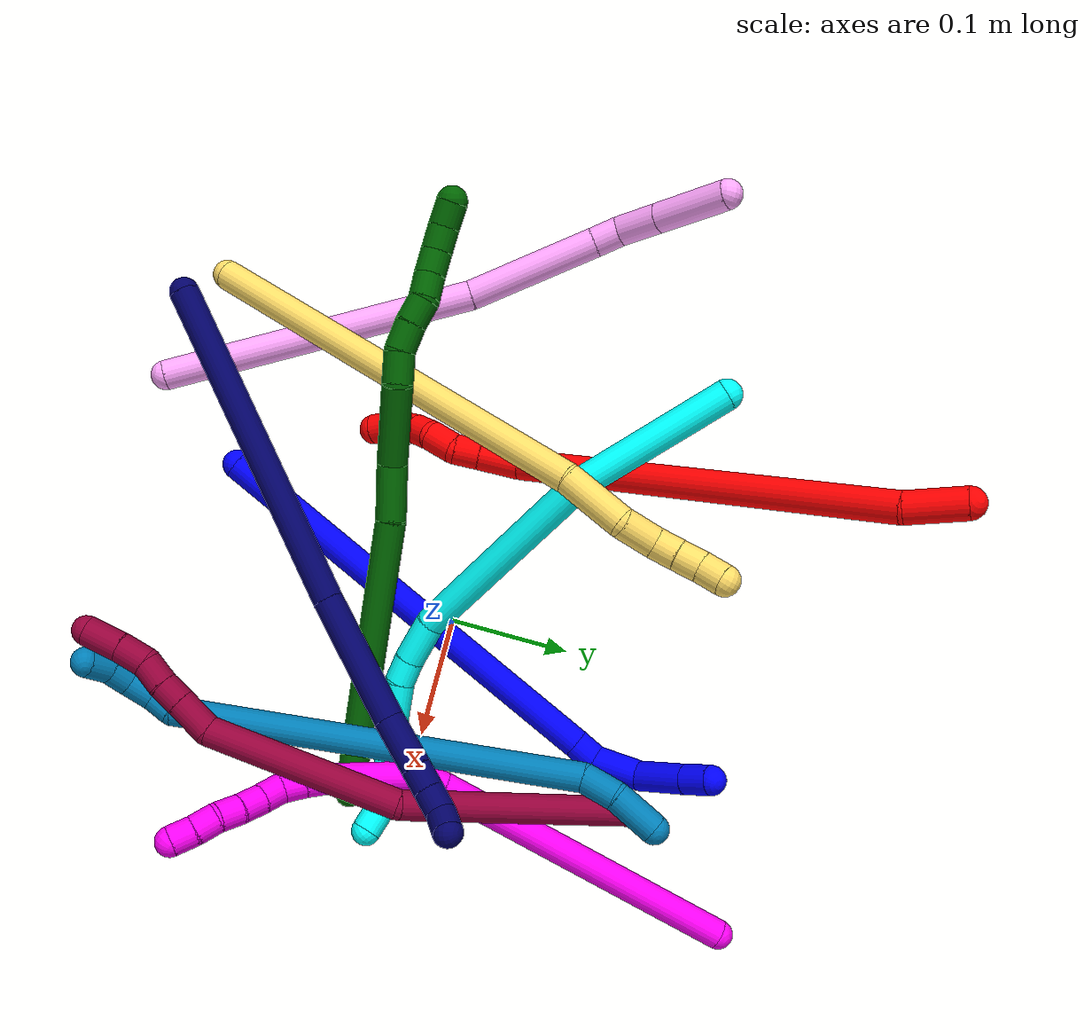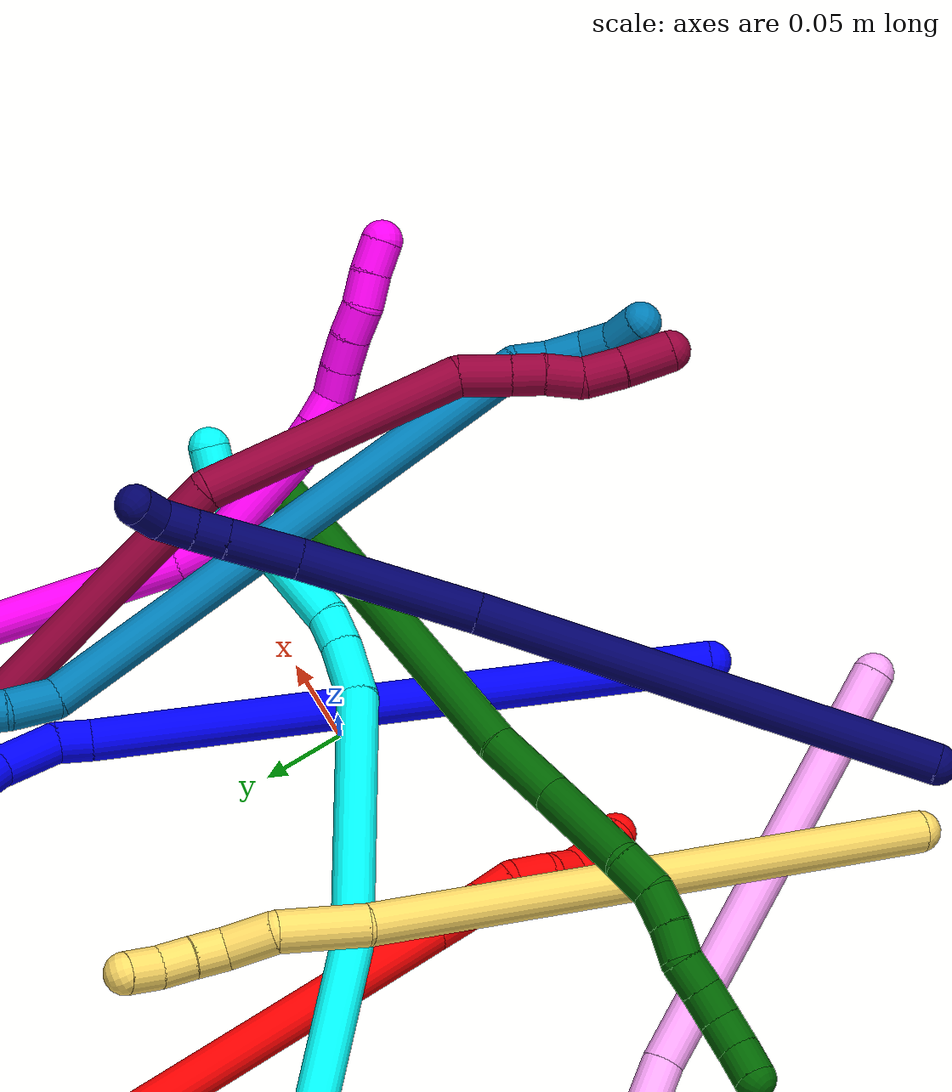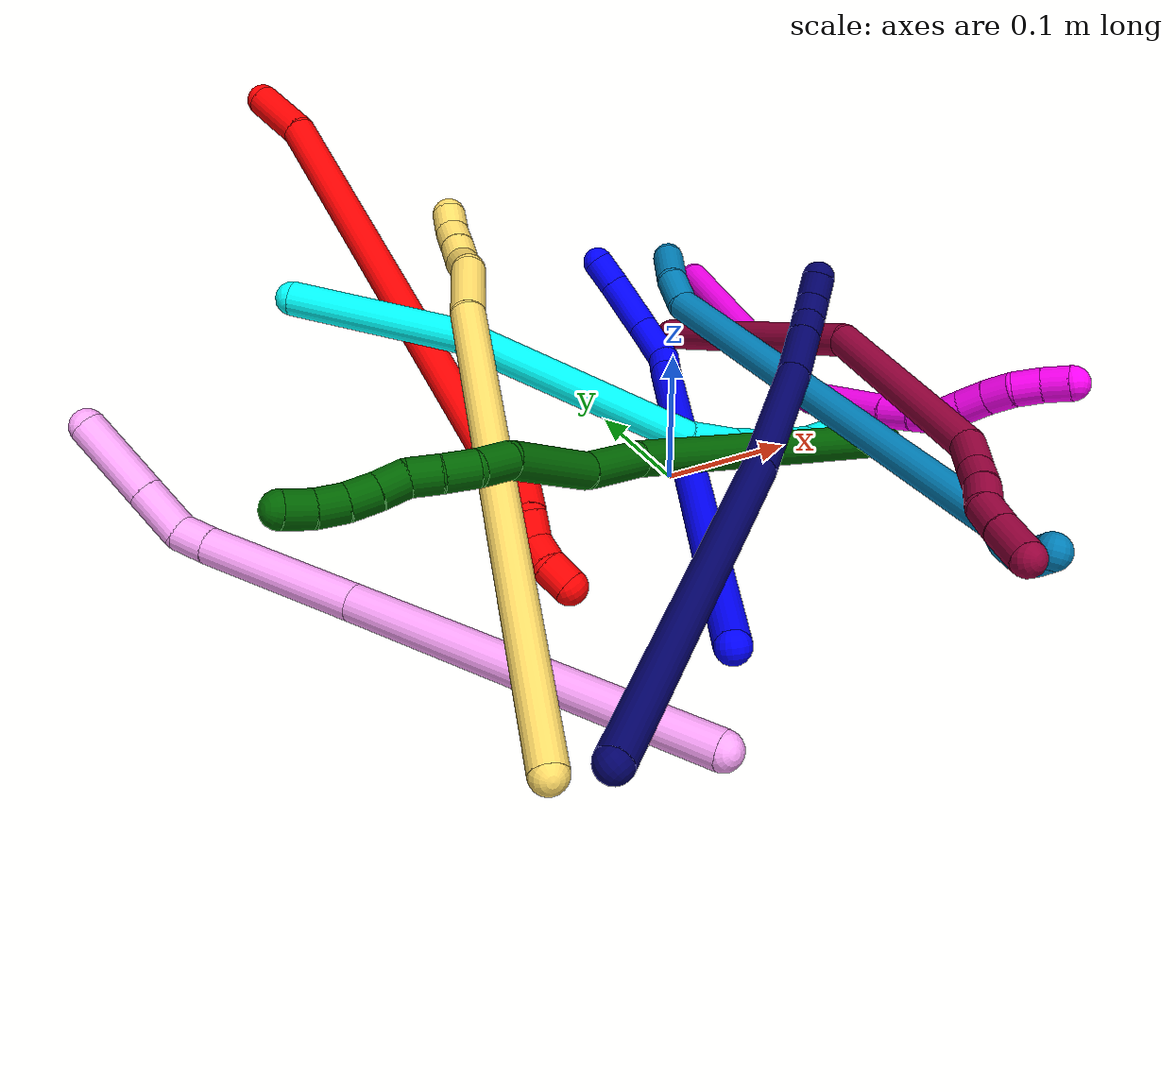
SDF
<sdf version="1.7">
 <world name="default">
  <plugin name="TubeGeneratorPlugin" filename="libtube_generator_plugin.so"/>
  <model name="photoneo_s_sensor">
   <static>1</static>
   <pose>0 0 2 1.57079 1.57079 3.14159</pose>
   <link name="link">
    <inertial><mass>0.1</mass></inertial>
    <sensor name="sensor" type="depth">
     <update_rate>30</update_rate>
     <camera>
      <horizontal_fov>1.22</horizontal_fov>
      <image><width>1920</width><height>1200</height><format>B8G8R8</format></image>
      <clip><near>0.1</near><far>2</far></clip>
      <depth_camera><output>points</output></depth_camera>
     </camera>
     <plugin name="camera_plugin" filename="libgazebo_ros_depth_camera.so">
      <baseline>0.2</baseline>
      <alwaysOn>1</alwaysOn>
      <updateRate>0.0</updateRate>
      <cameraName>camera_ir</cameraName>
      <imageTopicName>/camera/color/image_raw</imageTopicName>
      <cameraInfoTopicName>/camera/color/camera_info</cameraInfoTopicName>
      <depthImageTopicName>/camera/depth/image_raw</depthImageTopicName>
      <depthImageCameraInfoTopicName>/camera/depth/camera_info</depthImageCameraInfoTopicName>
      <pointCloudTopicName>/camera/depth/points</pointCloudTopicName>
      <frameName>fr_optical</frameName>
      <pointCloudCutoff>0.1</pointCloudCutoff>
      <pointCloudCutoffMax>2.0</pointCloudCutoffMax>
      <distortionK1>0</distortionK1>
      <distortionK2>0</distortionK2>
      <distortionK3>0</distortionK3>
      <distortionT1>0</distortionT1>
      <distortionT2>0</distortionT2>
      <CxPrime>0</CxPrime>
      <Cx>0</Cx>
      <Cy>0</Cy>
      <focalLength>0</focalLength>
      <hackBaseline>0</hackBaseline>
     </plugin>
    </sensor>
   </link>
  </model>
  <gravity>0 0 -9.8</gravity>
  <magnetic_field>6e-06 2.3e-05 -4.2e-05</magnetic_field>
  <atmosphere type="adiabatic"/>
  <physics name="default_physics" default="0" type="ode">
   <max_step_size>0.003</max_step_size>
   <real_time_factor>1</real_time_factor>
   <real_time_update_rate>1000</real_time_update_rate>
   <max_contacts>10000</max_contacts>
   <ode>
    <solver>
     <type>quick</type>
     <iters>100</iters>
     <sor>1.3</sor>
     <use_dynamic_moi_rescaling>0</use_dynamic_moi_rescaling>
    </solver>
    <constraints>
     <contact_max_correcting_vel>0</contact_max_correcting_vel>
     <contact_surface_layer>0.001</contact_surface_layer>
     <cfm>0</cfm>
     <erp>0.2</erp>
    </constraints>
   </ode>
  </physics>
  <scene><ambient>0.4 0.4 0.4 1</ambient><background>0.7 0.7 0.7 1</background><shadows>0</shadows></scene>
  <audio><device>default</device></audio>
  <spherical_coordinates>
   <surface_model>EARTH_WGS84</surface_model>
   <latitude_deg>0</latitude_deg>
   <longitude_deg>0</longitude_deg>
   <elevation>0</elevation>
   <heading_deg>0</heading_deg>
  </spherical_coordinates>
  <model name="bin">
   <static>1</static>
   <link name="bottom">
    <collision name="collision-bottom">
     <pose>0 0 -0.01 0 -0 0</pose>
     <geometry><box><size>0.8 0.6 0.02</size></box></geometry>
     <surface>
      <friction><ode><mu>100</mu><mu2>100</mu2></ode></friction>
      <contact><collide_bitmask>65535</collide_bitmask></contact>
     </surface>
    </collision>
   </link>
   <link name="west_wall">
    <collision name="collision-west_wall">
     <pose>-0.41 0 0.1 0 -0 0</pose>
     <geometry><box><size>0.02 0.6 0.2</size></box></geometry>
     <surface>
      <friction><ode><mu>100</mu><mu2>100</mu2></ode></friction>
      <contact><collide_bitmask>65535</collide_bitmask></contact>
     </surface>
    </collision>
   </link>
   <link name="east_wall">
    <collision name="collision-east_wall">
     <pose>0.41 0 0.1 0 -0 0</pose>
     <geometry><box><size>0.02 0.6 0.2</size></box></geometry>
     <surface>
      <friction><ode><mu>100</mu><mu2>100</mu2></ode></friction>
      <contact><collide_bitmask>65535</collide_bitmask></contact>
     </surface>
    </collision>
   </link>
   <link name="south_wall">
    <collision name="collision-south_wall">
     <pose>0 -0.31 0.1 0 -0 0</pose>
     <geometry><box><size>0.8 0.02 0.2</size></box></geometry>
     <surface>
      <friction><ode><mu>100</mu><mu2>100</mu2></ode></friction>
      <contact><collide_bitmask>65535</collide_bitmask></contact>
     </surface>
    </collision>
   </link>
   <link name="north_wall">
    <collision name="collision-north_wall">
     <pose>0 0.31 0.1 0 -0 0</pose>
     <geometry><box><size>0.8 0.02 0.2</size></box></geometry>
     <surface>
      <friction><ode><mu>100</mu><mu2>100</mu2></ode></friction>
      <contact><collide_bitmask>65535</collide_bitmask></contact>
     </surface>
    </collision>
   </link>
  </model>
  <model name="1">
   <static>0</static>
   <link name="1">
    <collision name="collision-cylinder-e_1_1_4">
     <pose>0.075033 0.143788 0.088297 -1.02009 0.418424 -0.236443</pose>
     <geometry><cylinder><radius>0.0125</radius><length>0.369331</length></cylinder></geometry>
     <surface>
      <friction><ode><mu>1.16</mu><mu2>1.16</mu2><slip1>0</slip1><slip2>0</slip2></ode></friction>
      <contact><ode><kp>1e+06</kp><kd>1</kd><max_vel>0</max_vel><min_depth>0.001</min_depth></ode></contact>
     </surface>
    </collision>
    <visual name="visual-cylinder-e_1_1_4">
     <pose>0.075033 0.143788 0.088297 -1.02009 0.418424 -0.236443</pose>
     <geometry><cylinder><radius>0.0125</radius><length>0.369331</length></cylinder></geometry>
     <material><ambient>0 0 1 1</ambient></material>
    </visual>
    <collision name="collision-cylinder-e_2_4_5">
     <pose>0.15447 0.295183 0.182902 -0.878465 0.419146 -0.199206</pose>
     <geometry><cylinder><radius>0.0125</radius><length>0.021638</length></cylinder></geometry>
     <surface>
      <friction><ode><mu>1.16</mu><mu2>1.16</mu2><slip1>0</slip1><slip2>0</slip2></ode></friction>
      <contact><ode><kp>1e+06</kp><kd>1</kd><max_vel>0</max_vel><min_depth>0.001</min_depth></ode></contact>
     </surface>
    </collision>
    <visual name="visual-cylinder-e_2_4_5">
     <pose>0.15447 0.295183 0.182902 -0.878465 0.419146 -0.199206</pose>
     <geometry><cylinder><radius>0.0125</radius><length>0.021638</length></cylinder></geometry>
     <material><ambient>0 0 1 1</ambient></material>
    </visual>
    <collision name="collision-cylinder-e_3_5_6">
     <pose>0.158737 0.316318 0.203863 -0.745521 -0.006815 0.002665</pose>
     <geometry><cylinder><radius>0.0125</radius><length>0.039886</length></cylinder></geometry>
     <surface>
      <friction><ode><mu>1.16</mu><mu2>1.16</mu2><slip1>0</slip1><slip2>0</slip2></ode></friction>
      <contact><ode><kp>1e+06</kp><kd>1</kd><max_vel>0</max_vel><min_depth>0.001</min_depth></ode></contact>
     </surface>
    </collision>
    <visual name="visual-cylinder-e_3_5_6">
     <pose>0.158737 0.316318 0.203863 -0.745521 -0.006815 0.002665</pose>
     <geometry><cylinder><radius>0.0125</radius><length>0.039886</length></cylinder></geometry>
     <material><ambient>0 0 1 1</ambient></material>
    </visual>
    <collision name="collision-cylinder-e_4_6_7">
     <pose>0.151721 0.337924 0.238417 -0.385568 -0.310004 0.060986</pose>
     <geometry><cylinder><radius>0.0125</radius><length>0.045107</length></cylinder></geometry>
     <surface>
      <friction><ode><mu>1.16</mu><mu2>1.16</mu2><slip1>0</slip1><slip2>0</slip2></ode></friction>
      <contact><ode><kp>1e+06</kp><kd>1</kd><max_vel>0</max_vel><min_depth>0.001</min_depth></ode></contact>
     </surface>
    </collision>
    <visual name="visual-cylinder-e_4_6_7">
     <pose>0.151721 0.337924 0.238417 -0.385568 -0.310004 0.060986</pose>
     <geometry><cylinder><radius>0.0125</radius><length>0.045107</length></cylinder></geometry>
     <material><ambient>0 0 1 1</ambient></material>
    </visual>
    <collision name="collision-cylinder-e_5_7_2">
     <pose>0.140802 0.350246 0.268813 -0.38432 -0.342714 0.067313</pose>
     <geometry><cylinder><radius>0.0125</radius><length>0.024038</length></cylinder></geometry>
     <surface>
      <friction><ode><mu>1.16</mu><mu2>1.16</mu2><slip1>0</slip1><slip2>0</slip2></ode></friction>
      <contact><ode><kp>1e+06</kp><kd>1</kd><max_vel>0</max_vel><min_depth>0.001</min_depth></ode></contact>
     </surface>
    </collision>
    <visual name="visual-cylinder-e_5_7_2">
     <pose>0.140802 0.350246 0.268813 -0.38432 -0.342714 0.067313</pose>
     <geometry><cylinder><radius>0.0125</radius><length>0.024038</length></cylinder></geometry>
     <material><ambient>0 0 1 1</ambient></material>
    </visual>
    <collision name="collision-sphere-2">
     <pose>0.136763 0.35449 0.279307 0 -0 0</pose>
     <geometry><sphere><radius>0.0125</radius></sphere></geometry>
     <surface>
      <friction><ode><mu>1.16</mu><mu2>1.16</mu2><slip1>0</slip1><slip2>0</slip2></ode></friction>
      <contact><ode><kp>1e+06</kp><kd>1</kd><max_vel>0</max_vel><min_depth>0.001</min_depth></ode></contact>
     </surface>
    </collision>
    <visual name="visual-sphere-2">
     <pose>0.136763 0.35449 0.279307 0 -0 0</pose>
     <geometry><sphere><radius>0.0125</radius></sphere></geometry>
     <material><ambient>0 0 1 1</ambient></material>
    </visual>
    <collision name="collision-sphere-7">
     <pose>0.144841 0.346002 0.258319 0 -0 0</pose>
     <geometry><sphere><radius>0.0125</radius></sphere></geometry>
     <surface>
      <friction><ode><mu>1.16</mu><mu2>1.16</mu2><slip1>0</slip1><slip2>0</slip2></ode></friction>
      <contact><ode><kp>1e+06</kp><kd>1</kd><max_vel>0</max_vel><min_depth>0.001</min_depth></ode></contact>
     </surface>
    </collision>
    <visual name="visual-sphere-7">
     <pose>0.144841 0.346002 0.258319 0 -0 0</pose>
     <geometry><sphere><radius>0.0125</radius></sphere></geometry>
     <material><ambient>0 0 1 1</ambient></material>
    </visual>
    <collision name="collision-sphere-6">
     <pose>0.158601 0.329847 0.218515 0 -0 0</pose>
     <geometry><sphere><radius>0.0125</radius></sphere></geometry>
     <surface>
      <friction><ode><mu>1.16</mu><mu2>1.16</mu2><slip1>0</slip1><slip2>0</slip2></ode></friction>
      <contact><ode><kp>1e+06</kp><kd>1</kd><max_vel>0</max_vel><min_depth>0.001</min_depth></ode></contact>
     </surface>
    </collision>
    <visual name="visual-sphere-6">
     <pose>0.158601 0.329847 0.218515 0 -0 0</pose>
     <geometry><sphere><radius>0.0125</radius></sphere></geometry>
     <material><ambient>0 0 1 1</ambient></material>
    </visual>
    <collision name="collision-sphere-5">
     <pose>0.158873 0.30279 0.18921 0 -0 0</pose>
     <geometry><sphere><radius>0.0125</radius></sphere></geometry>
     <surface>
      <friction><ode><mu>1.16</mu><mu2>1.16</mu2><slip1>0</slip1><slip2>0</slip2></ode></friction>
      <contact><ode><kp>1e+06</kp><kd>1</kd><max_vel>0</max_vel><min_depth>0.001</min_depth></ode></contact>
     </surface>
    </collision>
    <visual name="visual-sphere-5">
     <pose>0.158873 0.30279 0.18921 0 -0 0</pose>
     <geometry><sphere><radius>0.0125</radius></sphere></geometry>
     <material><ambient>0 0 1 1</ambient></material>
    </visual>
    <collision name="collision-sphere-1">
     <geometry><sphere><radius>0.0125</radius></sphere></geometry>
     <surface>
      <friction><ode><mu>1.16</mu><mu2>1.16</mu2><slip1>0</slip1><slip2>0</slip2></ode></friction>
      <contact><ode><kp>1e+06</kp><kd>1</kd><max_vel>0</max_vel><min_depth>0.001</min_depth></ode></contact>
     </surface>
    </collision>
    <visual name="visual-sphere-1">
     <geometry><sphere><radius>0.0125</radius></sphere></geometry>
     <material><ambient>0 0 1 1</ambient></material>
    </visual>
    <collision name="collision-sphere-4">
     <pose>0.150067 0.287576 0.176593 0 -0 0</pose>
     <geometry><sphere><radius>0.0125</radius></sphere></geometry>
     <surface>
      <friction><ode><mu>1.16</mu><mu2>1.16</mu2><slip1>0</slip1><slip2>0</slip2></ode></friction>
      <contact><ode><kp>1e+06</kp><kd>1</kd><max_vel>0</max_vel><min_depth>0.001</min_depth></ode></contact>
     </surface>
    </collision>
    <visual name="visual-sphere-4">
     <pose>0.150067 0.287576 0.176593 0 -0 0</pose>
     <geometry><sphere><radius>0.0125</radius></sphere></geometry>
     <material><ambient>0 0 1 1</ambient></material>
    </visual>
    <inertial>
     <pose>0.095229 0.191542 0.123831 0 -0 0</pose>
     <mass>0.5</mass>
     <inertia>
      <ixx>0.002871</ixx>
      <ixy>0</ixy>
      <ixz>0</ixz>
      <iyy>0.001628</iyy>
      <iyz>0</iyz>
      <izz>-0.004977</izz>
     </inertia>
    </inertial>
   </link>
   <pose>-0.078918 -0.209574 0.011946 -0.494642 0.124931 0.002539</pose>
  </model>
  <model name="2">
   <static>0</static>
   <link name="2">
    <collision name="collision-cylinder-e_1_1_4">
     <pose>0.006966 -0.015955 -0.014883 2.32145 0.309032 0.688093</pose>
     <geometry><cylinder><radius>0.0125</radius><length>0.045808</length></cylinder></geometry>
     <surface>
      <friction><ode><mu>1.16</mu><mu2>1.16</mu2><slip1>0</slip1><slip2>0</slip2></ode></friction>
      <contact><ode><kp>1e+06</kp><kd>1</kd><max_vel>0</max_vel><min_depth>0.001</min_depth></ode></contact>
     </surface>
    </collision>
    <visual name="visual-cylinder-e_1_1_4">
     <pose>0.006966 -0.015955 -0.014883 2.32145 0.309032 0.688093</pose>
     <geometry><cylinder><radius>0.0125</radius><length>0.045808</length></cylinder></geometry>
     <material><ambient>1 0 0 1</ambient></material>
    </visual>
    <collision name="collision-cylinder-e_2_4_5">
     <pose>0.021258 -0.141021 -0.142384 2.37201 0.046687 0.115176</pose>
     <geometry><cylinder><radius>0.0125</radius><length>0.313954</length></cylinder></geometry>
     <surface>
      <friction><ode><mu>1.16</mu><mu2>1.16</mu2><slip1>0</slip1><slip2>0</slip2></ode></friction>
      <contact><ode><kp>1e+06</kp><kd>1</kd><max_vel>0</max_vel><min_depth>0.001</min_depth></ode></contact>
     </surface>
    </collision>
    <visual name="visual-cylinder-e_2_4_5">
     <pose>0.021258 -0.141021 -0.142384 2.37201 0.046687 0.115176</pose>
     <geometry><cylinder><radius>0.0125</radius><length>0.313954</length></cylinder></geometry>
     <material><ambient>1 0 0 1</ambient></material>
    </visual>
    <collision name="collision-cylinder-e_3_5_6">
     <pose>0.031619 -0.266067 -0.261311 1.94777 0.17526 0.257118</pose>
     <geometry><cylinder><radius>0.0125</radius><length>0.034808</length></cylinder></geometry>
     <surface>
      <friction><ode><mu>1.16</mu><mu2>1.16</mu2><slip1>0</slip1><slip2>0</slip2></ode></friction>
      <contact><ode><kp>1e+06</kp><kd>1</kd><max_vel>0</max_vel><min_depth>0.001</min_depth></ode></contact>
     </surface>
    </collision>
    <visual name="visual-cylinder-e_3_5_6">
     <pose>0.031619 -0.266067 -0.261311 1.94777 0.17526 0.257118</pose>
     <geometry><cylinder><radius>0.0125</radius><length>0.034808</length></cylinder></geometry>
     <material><ambient>1 0 0 1</ambient></material>
    </visual>
    <collision name="collision-cylinder-e_4_6_7">
     <pose>0.037137 -0.291838 -0.270623 1.86716 0.236928 0.318851</pose>
     <geometry><cylinder><radius>0.0125</radius><length>0.021162</length></cylinder></geometry>
     <surface>
      <friction><ode><mu>1.16</mu><mu2>1.16</mu2><slip1>0</slip1><slip2>0</slip2></ode></friction>
      <contact><ode><kp>1e+06</kp><kd>1</kd><max_vel>0</max_vel><min_depth>0.001</min_depth></ode></contact>
     </surface>
    </collision>
    <visual name="visual-cylinder-e_4_6_7">
     <pose>0.037137 -0.291838 -0.270623 1.86716 0.236928 0.318851</pose>
     <geometry><cylinder><radius>0.0125</radius><length>0.021162</length></cylinder></geometry>
     <material><ambient>1 0 0 1</ambient></material>
    </visual>
    <collision name="collision-cylinder-e_5_7_8">
     <pose>0.037165 -0.311986 -0.279152 2.06267 -0.206951 -0.343489</pose>
     <geometry><cylinder><radius>0.0125</radius><length>0.023906</length></cylinder></geometry>
     <surface>
      <friction><ode><mu>1.16</mu><mu2>1.16</mu2><slip1>0</slip1><slip2>0</slip2></ode></friction>
      <contact><ode><kp>1e+06</kp><kd>1</kd><max_vel>0</max_vel><min_depth>0.001</min_depth></ode></contact>
     </surface>
    </collision>
    <visual name="visual-cylinder-e_5_7_8">
     <pose>0.037165 -0.311986 -0.279152 2.06267 -0.206951 -0.343489</pose>
     <geometry><cylinder><radius>0.0125</radius><length>0.023906</length></cylinder></geometry>
     <material><ambient>1 0 0 1</ambient></material>
    </visual>
    <collision name="collision-cylinder-e_6_8_9">
     <pose>0.031875 -0.328074 -0.292358 2.49676 -0.286687 -0.815633</pose>
     <geometry><cylinder><radius>0.0125</radius><length>0.020041</length></cylinder></geometry>
     <surface>
      <friction><ode><mu>1.16</mu><mu2>1.16</mu2><slip1>0</slip1><slip2>0</slip2></ode></friction>
      <contact><ode><kp>1e+06</kp><kd>1</kd><max_vel>0</max_vel><min_depth>0.001</min_depth></ode></contact>
     </surface>
    </collision>
    <visual name="visual-cylinder-e_6_8_9">
     <pose>0.031875 -0.328074 -0.292358 2.49676 -0.286687 -0.815633</pose>
     <geometry><cylinder><radius>0.0125</radius><length>0.020041</length></cylinder></geometry>
     <material><ambient>1 0 0 1</ambient></material>
    </visual>
    <collision name="collision-cylinder-e_7_9_10">
     <pose>0.02985 -0.341911 -0.305976 2.20569 0.080619 0.159267</pose>
     <geometry><cylinder><radius>0.0125</radius><length>0.020085</length></cylinder></geometry>
     <surface>
      <friction><ode><mu>1.16</mu><mu2>1.16</mu2><slip1>0</slip1><slip2>0</slip2></ode></friction>
      <contact><ode><kp>1e+06</kp><kd>1</kd><max_vel>0</max_vel><min_depth>0.001</min_depth></ode></contact>
     </surface>
    </collision>
    <visual name="visual-cylinder-e_7_9_10">
     <pose>0.02985 -0.341911 -0.305976 2.20569 0.080619 0.159267</pose>
     <geometry><cylinder><radius>0.0125</radius><length>0.020085</length></cylinder></geometry>
     <material><ambient>1 0 0 1</ambient></material>
    </visual>
    <collision name="collision-cylinder-e_8_10_2">
     <pose>0.033676 -0.356118 -0.319361 2.4516 0.302737 0.802815</pose>
     <geometry><cylinder><radius>0.0125</radius><length>0.020236</length></cylinder></geometry>
     <surface>
      <friction><ode><mu>1.16</mu><mu2>1.16</mu2><slip1>0</slip1><slip2>0</slip2></ode></friction>
      <contact><ode><kp>1e+06</kp><kd>1</kd><max_vel>0</max_vel><min_depth>0.001</min_depth></ode></contact>
     </surface>
    </collision>
    <visual name="visual-cylinder-e_8_10_2">
     <pose>0.033676 -0.356118 -0.319361 2.4516 0.302737 0.802815</pose>
     <geometry><cylinder><radius>0.0125</radius><length>0.020236</length></cylinder></geometry>
     <material><ambient>1 0 0 1</ambient></material>
    </visual>
    <collision name="collision-sphere-2">
     <pose>0.036692 -0.362265 -0.32681 0 -0 0</pose>
     <geometry><sphere><radius>0.0125</radius></sphere></geometry>
     <surface>
      <friction><ode><mu>1.16</mu><mu2>1.16</mu2><slip1>0</slip1><slip2>0</slip2></ode></friction>
      <contact><ode><kp>1e+06</kp><kd>1</kd><max_vel>0</max_vel><min_depth>0.001</min_depth></ode></contact>
     </surface>
    </collision>
    <visual name="visual-sphere-2">
     <pose>0.036692 -0.362265 -0.32681 0 -0 0</pose>
     <geometry><sphere><radius>0.0125</radius></sphere></geometry>
     <material><ambient>1 0 0 1</ambient></material>
    </visual>
    <collision name="collision-sphere-10">
     <pose>0.030659 -0.34997 -0.311913 0 -0 0</pose>
     <geometry><sphere><radius>0.0125</radius></sphere></geometry>
     <surface>
      <friction><ode><mu>1.16</mu><mu2>1.16</mu2><slip1>0</slip1><slip2>0</slip2></ode></friction>
      <contact><ode><kp>1e+06</kp><kd>1</kd><max_vel>0</max_vel><min_depth>0.001</min_depth></ode></contact>
     </surface>
    </collision>
    <visual name="visual-sphere-10">
     <pose>0.030659 -0.34997 -0.311913 0 -0 0</pose>
     <geometry><sphere><radius>0.0125</radius></sphere></geometry>
     <material><ambient>1 0 0 1</ambient></material>
    </visual>
    <collision name="collision-sphere-9">
     <pose>0.029042 -0.333852 -0.300039 0 -0 0</pose>
     <geometry><sphere><radius>0.0125</radius></sphere></geometry>
     <surface>
      <friction><ode><mu>1.16</mu><mu2>1.16</mu2><slip1>0</slip1><slip2>0</slip2></ode></friction>
      <contact><ode><kp>1e+06</kp><kd>1</kd><max_vel>0</max_vel><min_depth>0.001</min_depth></ode></contact>
     </surface>
    </collision>
    <visual name="visual-sphere-9">
     <pose>0.029042 -0.333852 -0.300039 0 -0 0</pose>
     <geometry><sphere><radius>0.0125</radius></sphere></geometry>
     <material><ambient>1 0 0 1</ambient></material>
    </visual>
    <collision name="collision-sphere-4">
     <pose>0.013932 -0.03191 -0.029766 0 -0 0</pose>
     <geometry><sphere><radius>0.0125</radius></sphere></geometry>
     <surface>
      <friction><ode><mu>1.16</mu><mu2>1.16</mu2><slip1>0</slip1><slip2>0</slip2></ode></friction>
      <contact><ode><kp>1e+06</kp><kd>1</kd><max_vel>0</max_vel><min_depth>0.001</min_depth></ode></contact>
     </surface>
    </collision>
    <visual name="visual-sphere-4">
     <pose>0.013932 -0.03191 -0.029766 0 -0 0</pose>
     <geometry><sphere><radius>0.0125</radius></sphere></geometry>
     <material><ambient>1 0 0 1</ambient></material>
    </visual>
    <collision name="collision-sphere-1">
     <geometry><sphere><radius>0.0125</radius></sphere></geometry>
     <surface>
      <friction><ode><mu>1.16</mu><mu2>1.16</mu2><slip1>0</slip1><slip2>0</slip2></ode></friction>
      <contact><ode><kp>1e+06</kp><kd>1</kd><max_vel>0</max_vel><min_depth>0.001</min_depth></ode></contact>
     </surface>
    </collision>
    <visual name="visual-sphere-1">
     <geometry><sphere><radius>0.0125</radius></sphere></geometry>
     <material><ambient>1 0 0 1</ambient></material>
    </visual>
    <collision name="collision-sphere-8">
     <pose>0.034709 -0.322297 -0.284676 0 -0 0</pose>
     <geometry><sphere><radius>0.0125</radius></sphere></geometry>
     <surface>
      <friction><ode><mu>1.16</mu><mu2>1.16</mu2><slip1>0</slip1><slip2>0</slip2></ode></friction>
      <contact><ode><kp>1e+06</kp><kd>1</kd><max_vel>0</max_vel><min_depth>0.001</min_depth></ode></contact>
     </surface>
    </collision>
    <visual name="visual-sphere-8">
     <pose>0.034709 -0.322297 -0.284676 0 -0 0</pose>
     <geometry><sphere><radius>0.0125</radius></sphere></geometry>
     <material><ambient>1 0 0 1</ambient></material>
    </visual>
    <collision name="collision-sphere-5">
     <pose>0.028584 -0.250133 -0.255003 0 -0 0</pose>
     <geometry><sphere><radius>0.0125</radius></sphere></geometry>
     <surface>
      <friction><ode><mu>1.16</mu><mu2>1.16</mu2><slip1>0</slip1><slip2>0</slip2></ode></friction>
      <contact><ode><kp>1e+06</kp><kd>1</kd><max_vel>0</max_vel><min_depth>0.001</min_depth></ode></contact>
     </surface>
    </collision>
    <visual name="visual-sphere-5">
     <pose>0.028584 -0.250133 -0.255003 0 -0 0</pose>
     <geometry><sphere><radius>0.0125</radius></sphere></geometry>
     <material><ambient>1 0 0 1</ambient></material>
    </visual>
    <collision name="collision-sphere-6">
     <pose>0.034654 -0.282001 -0.267619 0 -0 0</pose>
     <geometry><sphere><radius>0.0125</radius></sphere></geometry>
     <surface>
      <friction><ode><mu>1.16</mu><mu2>1.16</mu2><slip1>0</slip1><slip2>0</slip2></ode></friction>
      <contact><ode><kp>1e+06</kp><kd>1</kd><max_vel>0</max_vel><min_depth>0.001</min_depth></ode></contact>
     </surface>
    </collision>
    <visual name="visual-sphere-6">
     <pose>0.034654 -0.282001 -0.267619 0 -0 0</pose>
     <geometry><sphere><radius>0.0125</radius></sphere></geometry>
     <material><ambient>1 0 0 1</ambient></material>
    </visual>
    <collision name="collision-sphere-7">
     <pose>0.039621 -0.301675 -0.273627 0 -0 0</pose>
     <geometry><sphere><radius>0.0125</radius></sphere></geometry>
     <surface>
      <friction><ode><mu>1.16</mu><mu2>1.16</mu2><slip1>0</slip1><slip2>0</slip2></ode></friction>
      <contact><ode><kp>1e+06</kp><kd>1</kd><max_vel>0</max_vel><min_depth>0.001</min_depth></ode></contact>
     </surface>
    </collision>
    <visual name="visual-sphere-7">
     <pose>0.039621 -0.301675 -0.273627 0 -0 0</pose>
     <geometry><sphere><radius>0.0125</radius></sphere></geometry>
     <material><ambient>1 0 0 1</ambient></material>
    </visual>
    <inertial>
     <pose>0.023376 -0.177098 -0.170694 0 -0 0</pose>
     <mass>0.5</mass>
     <inertia>
      <ixx>0.002897</ixx>
      <ixy>0</ixy>
      <ixz>0</ixz>
      <iyy>-0.001571</iyy>
      <iyz>0</iyz>
      <izz>0.001668</izz>
     </inertia>
    </inertial>
   </link>
   <pose>-0.185042 0.331869 0.224131 -0.196769 -0.422812 -0.207319</pose>
  </model>
  <model name="3">
   <static>0</static>
   <link name="3">
    <collision name="collision-cylinder-e_1_1_4">
     <pose>0.064365 0.006994 0.005237 -0.928008 1.43588 -0.824153</pose>
     <geometry><cylinder><radius>0.0125</radius><length>0.12991</length></cylinder></geometry>
     <surface>
      <friction><ode><mu>1.16</mu><mu2>1.16</mu2><slip1>0</slip1><slip2>0</slip2></ode></friction>
      <contact><ode><kp>1e+06</kp><kd>1</kd><max_vel>0</max_vel><min_depth>0.001</min_depth></ode></contact>
     </surface>
    </collision>
    <visual name="visual-cylinder-e_1_1_4">
     <pose>0.064365 0.006994 0.005237 -0.928008 1.43588 -0.824153</pose>
     <geometry><cylinder><radius>0.0125</radius><length>0.12991</length></cylinder></geometry>
     <material><ambient>0.003922 1 0.996078 1</ambient></material>
    </visual>
    <collision name="collision-cylinder-e_2_4_5">
     <pose>0.215503 -0.009305 0.007753 1.68712 1.30685 1.42089</pose>
     <geometry><cylinder><radius>0.0125</radius><length>0.179773</length></cylinder></geometry>
     <surface>
      <friction><ode><mu>1.16</mu><mu2>1.16</mu2><slip1>0</slip1><slip2>0</slip2></ode></friction>
      <contact><ode><kp>1e+06</kp><kd>1</kd><max_vel>0</max_vel><min_depth>0.001</min_depth></ode></contact>
     </surface>
    </collision>
    <visual name="visual-cylinder-e_2_4_5">
     <pose>0.215503 -0.009305 0.007753 1.68712 1.30685 1.42089</pose>
     <geometry><cylinder><radius>0.0125</radius><length>0.179773</length></cylinder></geometry>
     <material><ambient>0.003922 1 0.996078 1</ambient></material>
    </visual>
    <collision name="collision-cylinder-e_3_5_6">
     <pose>0.319138 -0.036122 -0.001006 2.61307 1.17774 2.37177</pose>
     <geometry><cylinder><radius>0.0125</radius><length>0.036506</length></cylinder></geometry>
     <surface>
      <friction><ode><mu>1.16</mu><mu2>1.16</mu2><slip1>0</slip1><slip2>0</slip2></ode></friction>
      <contact><ode><kp>1e+06</kp><kd>1</kd><max_vel>0</max_vel><min_depth>0.001</min_depth></ode></contact>
     </surface>
    </collision>
    <visual name="visual-cylinder-e_3_5_6">
     <pose>0.319138 -0.036122 -0.001006 2.61307 1.17774 2.37177</pose>
     <geometry><cylinder><radius>0.0125</radius><length>0.036506</length></cylinder></geometry>
     <material><ambient>0.003922 1 0.996078 1</ambient></material>
    </visual>
    <collision name="collision-cylinder-e_4_6_7">
     <pose>0.345446 -0.04133 -0.011874 2.80645 1.07452 2.58825</pose>
     <geometry><cylinder><radius>0.0125</radius><length>0.021487</length></cylinder></geometry>
     <surface>
      <friction><ode><mu>1.16</mu><mu2>1.16</mu2><slip1>0</slip1><slip2>0</slip2></ode></friction>
      <contact><ode><kp>1e+06</kp><kd>1</kd><max_vel>0</max_vel><min_depth>0.001</min_depth></ode></contact>
     </surface>
    </collision>
    <visual name="visual-cylinder-e_4_6_7">
     <pose>0.345446 -0.04133 -0.011874 2.80645 1.07452 2.58825</pose>
     <geometry><cylinder><radius>0.0125</radius><length>0.021487</length></cylinder></geometry>
     <material><ambient>0.003922 1 0.996078 1</ambient></material>
    </visual>
    <collision name="collision-cylinder-e_5_7_8">
     <pose>0.372944 -0.049467 -0.031781 2.73707 0.833271 2.27374</pose>
     <geometry><cylinder><radius>0.0125</radius><length>0.048775</length></cylinder></geometry>
     <surface>
      <friction><ode><mu>1.16</mu><mu2>1.16</mu2><slip1>0</slip1><slip2>0</slip2></ode></friction>
      <contact><ode><kp>1e+06</kp><kd>1</kd><max_vel>0</max_vel><min_depth>0.001</min_depth></ode></contact>
     </surface>
    </collision>
    <visual name="visual-cylinder-e_5_7_8">
     <pose>0.372944 -0.049467 -0.031781 2.73707 0.833271 2.27374</pose>
     <geometry><cylinder><radius>0.0125</radius><length>0.048775</length></cylinder></geometry>
     <material><ambient>0.003922 1 0.996078 1</ambient></material>
    </visual>
    <collision name="collision-cylinder-e_6_8_9">
     <pose>0.397892 -0.057283 -0.054712 2.96998 0.713282 2.68778</pose>
     <geometry><cylinder><radius>0.0125</radius><length>0.021085</length></cylinder></geometry>
     <surface>
      <friction><ode><mu>1.16</mu><mu2>1.16</mu2><slip1>0</slip1><slip2>0</slip2></ode></friction>
      <contact><ode><kp>1e+06</kp><kd>1</kd><max_vel>0</max_vel><min_depth>0.001</min_depth></ode></contact>
     </surface>
    </collision>
    <visual name="visual-cylinder-e_6_8_9">
     <pose>0.397892 -0.057283 -0.054712 2.96998 0.713282 2.68778</pose>
     <geometry><cylinder><radius>0.0125</radius><length>0.021085</length></cylinder></geometry>
     <material><ambient>0.003922 1 0.996078 1</ambient></material>
    </visual>
    <collision name="collision-cylinder-e_7_9_10">
     <pose>0.412728 -0.057842 -0.069663 -3.02895 0.838211 -2.88982</pose>
     <geometry><cylinder><radius>0.0125</radius><length>0.021354</length></cylinder></geometry>
     <surface>
      <friction><ode><mu>1.16</mu><mu2>1.16</mu2><slip1>0</slip1><slip2>0</slip2></ode></friction>
      <contact><ode><kp>1e+06</kp><kd>1</kd><max_vel>0</max_vel><min_depth>0.001</min_depth></ode></contact>
     </surface>
    </collision>
    <visual name="visual-cylinder-e_7_9_10">
     <pose>0.412728 -0.057842 -0.069663 -3.02895 0.838211 -2.88982</pose>
     <geometry><cylinder><radius>0.0125</radius><length>0.021354</length></cylinder></geometry>
     <material><ambient>0.003922 1 0.996078 1</ambient></material>
    </visual>
    <collision name="collision-cylinder-e_8_10_11">
     <pose>0.42775 -0.056226 -0.084239 -3.0332 0.755312 -2.86977</pose>
     <geometry><cylinder><radius>0.0125</radius><length>0.020669</length></cylinder></geometry>
     <surface>
      <friction><ode><mu>1.16</mu><mu2>1.16</mu2><slip1>0</slip1><slip2>0</slip2></ode></friction>
      <contact><ode><kp>1e+06</kp><kd>1</kd><max_vel>0</max_vel><min_depth>0.001</min_depth></ode></contact>
     </surface>
    </collision>
    <visual name="visual-cylinder-e_8_10_11">
     <pose>0.42775 -0.056226 -0.084239 -3.0332 0.755312 -2.86977</pose>
     <geometry><cylinder><radius>0.0125</radius><length>0.020669</length></cylinder></geometry>
     <material><ambient>0.003922 1 0.996078 1</ambient></material>
    </visual>
    <collision name="collision-cylinder-e_9_11_2">
     <pose>0.44353 -0.052214 -0.096033 -2.50371 1.01754 -2.07248</pose>
     <geometry><cylinder><radius>0.0125</radius><length>0.020441</length></cylinder></geometry>
     <surface>
      <friction><ode><mu>1.16</mu><mu2>1.16</mu2><slip1>0</slip1><slip2>0</slip2></ode></friction>
      <contact><ode><kp>1e+06</kp><kd>1</kd><max_vel>0</max_vel><min_depth>0.001</min_depth></ode></contact>
     </surface>
    </collision>
    <visual name="visual-cylinder-e_9_11_2">
     <pose>0.44353 -0.052214 -0.096033 -2.50371 1.01754 -2.07248</pose>
     <geometry><cylinder><radius>0.0125</radius><length>0.020441</length></cylinder></geometry>
     <material><ambient>0.003922 1 0.996078 1</ambient></material>
    </visual>
    <collision name="collision-sphere-2">
     <pose>0.452226 -0.049015 -0.100347 0 -0 0</pose>
     <geometry><sphere><radius>0.0125</radius></sphere></geometry>
     <surface>
      <friction><ode><mu>1.16</mu><mu2>1.16</mu2><slip1>0</slip1><slip2>0</slip2></ode></friction>
      <contact><ode><kp>1e+06</kp><kd>1</kd><max_vel>0</max_vel><min_depth>0.001</min_depth></ode></contact>
     </surface>
    </collision>
    <visual name="visual-sphere-2">
     <pose>0.452226 -0.049015 -0.100347 0 -0 0</pose>
     <geometry><sphere><radius>0.0125</radius></sphere></geometry>
     <material><ambient>0.003922 1 0.996078 1</ambient></material>
    </visual>
    <collision name="collision-sphere-11">
     <pose>0.434835 -0.055412 -0.091718 0 -0 0</pose>
     <geometry><sphere><radius>0.0125</radius></sphere></geometry>
     <surface>
      <friction><ode><mu>1.16</mu><mu2>1.16</mu2><slip1>0</slip1><slip2>0</slip2></ode></friction>
      <contact><ode><kp>1e+06</kp><kd>1</kd><max_vel>0</max_vel><min_depth>0.001</min_depth></ode></contact>
     </surface>
    </collision>
    <visual name="visual-sphere-11">
     <pose>0.434835 -0.055412 -0.091718 0 -0 0</pose>
     <geometry><sphere><radius>0.0125</radius></sphere></geometry>
     <material><ambient>0.003922 1 0.996078 1</ambient></material>
    </visual>
    <collision name="collision-sphere-10">
     <pose>0.420666 -0.05704 -0.076759 0 -0 0</pose>
     <geometry><sphere><radius>0.0125</radius></sphere></geometry>
     <surface>
      <friction><ode><mu>1.16</mu><mu2>1.16</mu2><slip1>0</slip1><slip2>0</slip2></ode></friction>
      <contact><ode><kp>1e+06</kp><kd>1</kd><max_vel>0</max_vel><min_depth>0.001</min_depth></ode></contact>
     </surface>
    </collision>
    <visual name="visual-sphere-10">
     <pose>0.420666 -0.05704 -0.076759 0 -0 0</pose>
     <geometry><sphere><radius>0.0125</radius></sphere></geometry>
     <material><ambient>0.003922 1 0.996078 1</ambient></material>
    </visual>
    <collision name="collision-sphere-9">
     <pose>0.40479 -0.058645 -0.062568 0 -0 0</pose>
     <geometry><sphere><radius>0.0125</radius></sphere></geometry>
     <surface>
      <friction><ode><mu>1.16</mu><mu2>1.16</mu2><slip1>0</slip1><slip2>0</slip2></ode></friction>
      <contact><ode><kp>1e+06</kp><kd>1</kd><max_vel>0</max_vel><min_depth>0.001</min_depth></ode></contact>
     </surface>
    </collision>
    <visual name="visual-sphere-9">
     <pose>0.40479 -0.058645 -0.062568 0 -0 0</pose>
     <geometry><sphere><radius>0.0125</radius></sphere></geometry>
     <material><ambient>0.003922 1 0.996078 1</ambient></material>
    </visual>
    <collision name="collision-sphere-4">
     <pose>0.128729 0.013987 0.010475 0 -0 0</pose>
     <geometry><sphere><radius>0.0125</radius></sphere></geometry>
     <surface>
      <friction><ode><mu>1.16</mu><mu2>1.16</mu2><slip1>0</slip1><slip2>0</slip2></ode></friction>
      <contact><ode><kp>1e+06</kp><kd>1</kd><max_vel>0</max_vel><min_depth>0.001</min_depth></ode></contact>
     </surface>
    </collision>
    <visual name="visual-sphere-4">
     <pose>0.128729 0.013987 0.010475 0 -0 0</pose>
     <geometry><sphere><radius>0.0125</radius></sphere></geometry>
     <material><ambient>0.003922 1 0.996078 1</ambient></material>
    </visual>
    <collision name="collision-sphere-1">
     <geometry><sphere><radius>0.0125</radius></sphere></geometry>
     <surface>
      <friction><ode><mu>1.16</mu><mu2>1.16</mu2><slip1>0</slip1><slip2>0</slip2></ode></friction>
      <contact><ode><kp>1e+06</kp><kd>1</kd><max_vel>0</max_vel><min_depth>0.001</min_depth></ode></contact>
     </surface>
    </collision>
    <visual name="visual-sphere-1">
     <geometry><sphere><radius>0.0125</radius></sphere></geometry>
     <material><ambient>0.003922 1 0.996078 1</ambient></material>
    </visual>
    <collision name="collision-sphere-8">
     <pose>0.390994 -0.055922 -0.046857 0 -0 0</pose>
     <geometry><sphere><radius>0.0125</radius></sphere></geometry>
     <surface>
      <friction><ode><mu>1.16</mu><mu2>1.16</mu2><slip1>0</slip1><slip2>0</slip2></ode></friction>
      <contact><ode><kp>1e+06</kp><kd>1</kd><max_vel>0</max_vel><min_depth>0.001</min_depth></ode></contact>
     </surface>
    </collision>
    <visual name="visual-sphere-8">
     <pose>0.390994 -0.055922 -0.046857 0 -0 0</pose>
     <geometry><sphere><radius>0.0125</radius></sphere></geometry>
     <material><ambient>0.003922 1 0.996078 1</ambient></material>
    </visual>
    <collision name="collision-sphere-5">
     <pose>0.302277 -0.032597 0.005031 0 -0 0</pose>
     <geometry><sphere><radius>0.0125</radius></sphere></geometry>
     <surface>
      <friction><ode><mu>1.16</mu><mu2>1.16</mu2><slip1>0</slip1><slip2>0</slip2></ode></friction>
      <contact><ode><kp>1e+06</kp><kd>1</kd><max_vel>0</max_vel><min_depth>0.001</min_depth></ode></contact>
     </surface>
    </collision>
    <visual name="visual-sphere-5">
     <pose>0.302277 -0.032597 0.005031 0 -0 0</pose>
     <geometry><sphere><radius>0.0125</radius></sphere></geometry>
     <material><ambient>0.003922 1 0.996078 1</ambient></material>
    </visual>
    <collision name="collision-sphere-6">
     <pose>0.335999 -0.039648 -0.007043 0 -0 0</pose>
     <geometry><sphere><radius>0.0125</radius></sphere></geometry>
     <surface>
      <friction><ode><mu>1.16</mu><mu2>1.16</mu2><slip1>0</slip1><slip2>0</slip2></ode></friction>
      <contact><ode><kp>1e+06</kp><kd>1</kd><max_vel>0</max_vel><min_depth>0.001</min_depth></ode></contact>
     </surface>
    </collision>
    <visual name="visual-sphere-6">
     <pose>0.335999 -0.039648 -0.007043 0 -0 0</pose>
     <geometry><sphere><radius>0.0125</radius></sphere></geometry>
     <material><ambient>0.003922 1 0.996078 1</ambient></material>
    </visual>
    <collision name="collision-sphere-7">
     <pose>0.354894 -0.043013 -0.016705 0 -0 0</pose>
     <geometry><sphere><radius>0.0125</radius></sphere></geometry>
     <surface>
      <friction><ode><mu>1.16</mu><mu2>1.16</mu2><slip1>0</slip1><slip2>0</slip2></ode></friction>
      <contact><ode><kp>1e+06</kp><kd>1</kd><max_vel>0</max_vel><min_depth>0.001</min_depth></ode></contact>
     </surface>
    </collision>
    <visual name="visual-sphere-7">
     <pose>0.354894 -0.043013 -0.016705 0 -0 0</pose>
     <geometry><sphere><radius>0.0125</radius></sphere></geometry>
     <material><ambient>0.003922 1 0.996078 1</ambient></material>
    </visual>
    <inertial>
     <pose>0.238954 -0.020112 -0.012226 0 -0 0</pose>
     <mass>0.5</mass>
     <inertia>
      <ixx>0.000176</ixx>
      <ixy>0</ixy>
      <ixz>0</ixz>
      <iyy>0.000776</iyy>
      <iyz>0</iyz>
      <izz>-0.000577</izz>
     </inertia>
    </inertial>
   </link>
   <pose>-0.227195 0.158285 0.129873 1.80975 0.191334 -0.654758</pose>
  </model>
  <model name="4">
   <static>0</static>
   <link name="4">
    <collision name="collision-cylinder-e_1_1_4">
     <pose>-0.076999 -0.005274 0.108368 0.048633 -0.6172 -0.015506</pose>
     <geometry><cylinder><radius>0.0125</radius><length>0.266085</length></cylinder></geometry>
     <surface>
      <friction><ode><mu>1.16</mu><mu2>1.16</mu2><slip1>0</slip1><slip2>0</slip2></ode></friction>
      <contact><ode><kp>1e+06</kp><kd>1</kd><max_vel>0</max_vel><min_depth>0.001</min_depth></ode></contact>
     </surface>
    </collision>
    <visual name="visual-cylinder-e_1_1_4">
     <pose>-0.076999 -0.005274 0.108368 0.048633 -0.6172 -0.015506</pose>
     <geometry><cylinder><radius>0.0125</radius><length>0.266085</length></cylinder></geometry>
     <material><ambient>1 0.65098 0.996078 1</ambient></material>
    </visual>
    <collision name="collision-cylinder-e_2_4_5">
     <pose>-0.193689 -0.012283 0.256062 0.044064 -0.789537 -0.018361</pose>
     <geometry><cylinder><radius>0.0125</radius><length>0.111803</length></cylinder></geometry>
     <surface>
      <friction><ode><mu>1.16</mu><mu2>1.16</mu2><slip1>0</slip1><slip2>0</slip2></ode></friction>
      <contact><ode><kp>1e+06</kp><kd>1</kd><max_vel>0</max_vel><min_depth>0.001</min_depth></ode></contact>
     </surface>
    </collision>
    <visual name="visual-cylinder-e_2_4_5">
     <pose>-0.193689 -0.012283 0.256062 0.044064 -0.789537 -0.018361</pose>
     <geometry><cylinder><radius>0.0125</radius><length>0.111803</length></cylinder></geometry>
     <material><ambient>1 0.65098 0.996078 1</ambient></material>
    </visual>
    <collision name="collision-cylinder-e_3_5_6">
     <pose>-0.242052 -0.014981 0.303131 0.123864 -0.838082 -0.055229</pose>
     <geometry><cylinder><radius>0.0125</radius><length>0.023329</length></cylinder></geometry>
     <surface>
      <friction><ode><mu>1.16</mu><mu2>1.16</mu2><slip1>0</slip1><slip2>0</slip2></ode></friction>
      <contact><ode><kp>1e+06</kp><kd>1</kd><max_vel>0</max_vel><min_depth>0.001</min_depth></ode></contact>
     </surface>
    </collision>
    <visual name="visual-cylinder-e_3_5_6">
     <pose>-0.242052 -0.014981 0.303131 0.123864 -0.838082 -0.055229</pose>
     <geometry><cylinder><radius>0.0125</radius><length>0.023329</length></cylinder></geometry>
     <material><ambient>1 0.65098 0.996078 1</ambient></material>
    </visual>
    <collision name="collision-cylinder-e_4_6_7">
     <pose>-0.264781 -0.024219 0.319273 0.777838 -0.872897 -0.377738</pose>
     <geometry><cylinder><radius>0.0125</radius><length>0.036696</length></cylinder></geometry>
     <surface>
      <friction><ode><mu>1.16</mu><mu2>1.16</mu2><slip1>0</slip1><slip2>0</slip2></ode></friction>
      <contact><ode><kp>1e+06</kp><kd>1</kd><max_vel>0</max_vel><min_depth>0.001</min_depth></ode></contact>
     </surface>
    </collision>
    <visual name="visual-cylinder-e_4_6_7">
     <pose>-0.264781 -0.024219 0.319273 0.777838 -0.872897 -0.377738</pose>
     <geometry><cylinder><radius>0.0125</radius><length>0.036696</length></cylinder></geometry>
     <material><ambient>1 0.65098 0.996078 1</ambient></material>
    </visual>
    <collision name="collision-cylinder-e_5_7_2">
     <pose>-0.30264 -0.046511 0.341841 0.780117 -0.873658 -0.379303</pose>
     <geometry><cylinder><radius>0.0125</radius><length>0.062087</length></cylinder></geometry>
     <surface>
      <friction><ode><mu>1.16</mu><mu2>1.16</mu2><slip1>0</slip1><slip2>0</slip2></ode></friction>
      <contact><ode><kp>1e+06</kp><kd>1</kd><max_vel>0</max_vel><min_depth>0.001</min_depth></ode></contact>
     </surface>
    </collision>
    <visual name="visual-cylinder-e_5_7_2">
     <pose>-0.30264 -0.046511 0.341841 0.780117 -0.873658 -0.379303</pose>
     <geometry><cylinder><radius>0.0125</radius><length>0.062087</length></cylinder></geometry>
     <material><ambient>1 0.65098 0.996078 1</ambient></material>
    </visual>
    <collision name="collision-sphere-2">
     <pose>-0.32644 -0.06053 0.356008 0 -0 0</pose>
     <geometry><sphere><radius>0.0125</radius></sphere></geometry>
     <surface>
      <friction><ode><mu>1.16</mu><mu2>1.16</mu2><slip1>0</slip1><slip2>0</slip2></ode></friction>
      <contact><ode><kp>1e+06</kp><kd>1</kd><max_vel>0</max_vel><min_depth>0.001</min_depth></ode></contact>
     </surface>
    </collision>
    <visual name="visual-sphere-2">
     <pose>-0.32644 -0.06053 0.356008 0 -0 0</pose>
     <geometry><sphere><radius>0.0125</radius></sphere></geometry>
     <material><ambient>1 0.65098 0.996078 1</ambient></material>
    </visual>
    <collision name="collision-sphere-7">
     <pose>-0.278839 -0.032493 0.327673 0 -0 0</pose>
     <geometry><sphere><radius>0.0125</radius></sphere></geometry>
     <surface>
      <friction><ode><mu>1.16</mu><mu2>1.16</mu2><slip1>0</slip1><slip2>0</slip2></ode></friction>
      <contact><ode><kp>1e+06</kp><kd>1</kd><max_vel>0</max_vel><min_depth>0.001</min_depth></ode></contact>
     </surface>
    </collision>
    <visual name="visual-sphere-7">
     <pose>-0.278839 -0.032493 0.327673 0 -0 0</pose>
     <geometry><sphere><radius>0.0125</radius></sphere></geometry>
     <material><ambient>1 0.65098 0.996078 1</ambient></material>
    </visual>
    <collision name="collision-sphere-6">
     <pose>-0.250723 -0.015945 0.310873 0 -0 0</pose>
     <geometry><sphere><radius>0.0125</radius></sphere></geometry>
     <surface>
      <friction><ode><mu>1.16</mu><mu2>1.16</mu2><slip1>0</slip1><slip2>0</slip2></ode></friction>
      <contact><ode><kp>1e+06</kp><kd>1</kd><max_vel>0</max_vel><min_depth>0.001</min_depth></ode></contact>
     </surface>
    </collision>
    <visual name="visual-sphere-6">
     <pose>-0.250723 -0.015945 0.310873 0 -0 0</pose>
     <geometry><sphere><radius>0.0125</radius></sphere></geometry>
     <material><ambient>1 0.65098 0.996078 1</ambient></material>
    </visual>
    <collision name="collision-sphere-5">
     <pose>-0.233381 -0.014017 0.295388 0 -0 0</pose>
     <geometry><sphere><radius>0.0125</radius></sphere></geometry>
     <surface>
      <friction><ode><mu>1.16</mu><mu2>1.16</mu2><slip1>0</slip1><slip2>0</slip2></ode></friction>
      <contact><ode><kp>1e+06</kp><kd>1</kd><max_vel>0</max_vel><min_depth>0.001</min_depth></ode></contact>
     </surface>
    </collision>
    <visual name="visual-sphere-5">
     <pose>-0.233381 -0.014017 0.295388 0 -0 0</pose>
     <geometry><sphere><radius>0.0125</radius></sphere></geometry>
     <material><ambient>1 0.65098 0.996078 1</ambient></material>
    </visual>
    <collision name="collision-sphere-1">
     <geometry><sphere><radius>0.0125</radius></sphere></geometry>
     <surface>
      <friction><ode><mu>1.16</mu><mu2>1.16</mu2><slip1>0</slip1><slip2>0</slip2></ode></friction>
      <contact><ode><kp>1e+06</kp><kd>1</kd><max_vel>0</max_vel><min_depth>0.001</min_depth></ode></contact>
     </surface>
    </collision>
    <visual name="visual-sphere-1">
     <geometry><sphere><radius>0.0125</radius></sphere></geometry>
     <material><ambient>1 0.65098 0.996078 1</ambient></material>
    </visual>
    <collision name="collision-sphere-4">
     <pose>-0.153998 -0.010549 0.216736 0 -0 0</pose>
     <geometry><sphere><radius>0.0125</radius></sphere></geometry>
     <surface>
      <friction><ode><mu>1.16</mu><mu2>1.16</mu2><slip1>0</slip1><slip2>0</slip2></ode></friction>
      <contact><ode><kp>1e+06</kp><kd>1</kd><max_vel>0</max_vel><min_depth>0.001</min_depth></ode></contact>
     </surface>
    </collision>
    <visual name="visual-sphere-4">
     <pose>-0.153998 -0.010549 0.216736 0 -0 0</pose>
     <geometry><sphere><radius>0.0125</radius></sphere></geometry>
     <material><ambient>1 0.65098 0.996078 1</ambient></material>
    </visual>
    <inertial>
     <pose>-0.152593 -0.013805 0.194951 0 -0 0</pose>
     <mass>0.5</mass>
     <inertia>
      <ixx>0.001338</ixx>
      <ixy>0</ixy>
      <ixz>0</ixz>
      <iyy>0.001693</iyy>
      <iyz>0</iyz>
      <izz>0.00113</izz>
     </inertia>
    </inertial>
   </link>
   <pose>-0.135562 -0.287977 0.011489 -2.1194 0.594149 -0.248176</pose>
  </model>
  <model name="5">
   <static>0</static>
   <link name="5">
    <collision name="collision-cylinder-e_1_1_4">
     <pose>0.016371 0.110228 -0.138809 -2.47046 0.092101 -0.26275</pose>
     <geometry><cylinder><radius>0.0125</radius><length>0.356012</length></cylinder></geometry>
     <surface>
      <friction><ode><mu>1.16</mu><mu2>1.16</mu2><slip1>0</slip1><slip2>0</slip2></ode></friction>
      <contact><ode><kp>1e+06</kp><kd>1</kd><max_vel>0</max_vel><min_depth>0.001</min_depth></ode></contact>
     </surface>
    </collision>
    <visual name="visual-cylinder-e_1_1_4">
     <pose>0.016371 0.110228 -0.138809 -2.47046 0.092101 -0.26275</pose>
     <geometry><cylinder><radius>0.0125</radius><length>0.356012</length></cylinder></geometry>
     <material><ambient>1 0.858824 0.4 1</ambient></material>
    </visual>
    <collision name="collision-cylinder-e_2_4_5">
     <pose>0.038517 0.233077 -0.30019 -2.63173 0.219681 -0.800682</pose>
     <geometry><cylinder><radius>0.0125</radius><length>0.052995</length></cylinder></geometry>
     <surface>
      <friction><ode><mu>1.16</mu><mu2>1.16</mu2><slip1>0</slip1><slip2>0</slip2></ode></friction>
      <contact><ode><kp>1e+06</kp><kd>1</kd><max_vel>0</max_vel><min_depth>0.001</min_depth></ode></contact>
     </surface>
    </collision>
    <visual name="visual-cylinder-e_2_4_5">
     <pose>0.038517 0.233077 -0.30019 -2.63173 0.219681 -0.800682</pose>
     <geometry><cylinder><radius>0.0125</radius><length>0.052995</length></cylinder></geometry>
     <material><ambient>1 0.858824 0.4 1</ambient></material>
    </visual>
    <collision name="collision-cylinder-e_3_5_6">
     <pose>0.044945 0.246969 -0.337915 -3.05792 0.04297 -0.948504</pose>
     <geometry><cylinder><radius>0.0125</radius><length>0.030442</length></cylinder></geometry>
     <surface>
      <friction><ode><mu>1.16</mu><mu2>1.16</mu2><slip1>0</slip1><slip2>0</slip2></ode></friction>
      <contact><ode><kp>1e+06</kp><kd>1</kd><max_vel>0</max_vel><min_depth>0.001</min_depth></ode></contact>
     </surface>
    </collision>
    <visual name="visual-cylinder-e_3_5_6">
     <pose>0.044945 0.246969 -0.337915 -3.05792 0.04297 -0.948504</pose>
     <geometry><cylinder><radius>0.0125</radius><length>0.030442</length></cylinder></geometry>
     <material><ambient>1 0.858824 0.4 1</ambient></material>
    </visual>
    <collision name="collision-cylinder-e_4_6_7">
     <pose>0.04587 0.253556 -0.361663 -2.58768 0.026806 -0.094236</pose>
     <geometry><cylinder><radius>0.0125</radius><length>0.020218</length></cylinder></geometry>
     <surface>
      <friction><ode><mu>1.16</mu><mu2>1.16</mu2><slip1>0</slip1><slip2>0</slip2></ode></friction>
      <contact><ode><kp>1e+06</kp><kd>1</kd><max_vel>0</max_vel><min_depth>0.001</min_depth></ode></contact>
     </surface>
    </collision>
    <visual name="visual-cylinder-e_4_6_7">
     <pose>0.04587 0.253556 -0.361663 -2.58768 0.026806 -0.094236</pose>
     <geometry><cylinder><radius>0.0125</radius><length>0.020218</length></cylinder></geometry>
     <material><ambient>1 0.858824 0.4 1</ambient></material>
    </visual>
    <collision name="collision-cylinder-e_5_7_8">
     <pose>0.046236 0.263699 -0.379066 -2.64027 0.009485 -0.03704</pose>
     <geometry><cylinder><radius>0.0125</radius><length>0.020089</length></cylinder></geometry>
     <surface>
      <friction><ode><mu>1.16</mu><mu2>1.16</mu2><slip1>0</slip1><slip2>0</slip2></ode></friction>
      <contact><ode><kp>1e+06</kp><kd>1</kd><max_vel>0</max_vel><min_depth>0.001</min_depth></ode></contact>
     </surface>
    </collision>
    <visual name="visual-cylinder-e_5_7_8">
     <pose>0.046236 0.263699 -0.379066 -2.64027 0.009485 -0.03704</pose>
     <geometry><cylinder><radius>0.0125</radius><length>0.020089</length></cylinder></geometry>
     <material><ambient>1 0.858824 0.4 1</ambient></material>
    </visual>
    <collision name="collision-cylinder-e_6_8_2">
     <pose>0.047175 0.275075 -0.395545 -2.43486 0.083393 -0.225266</pose>
     <geometry><cylinder><radius>0.0125</radius><length>0.020243</length></cylinder></geometry>
     <surface>
      <friction><ode><mu>1.16</mu><mu2>1.16</mu2><slip1>0</slip1><slip2>0</slip2></ode></friction>
      <contact><ode><kp>1e+06</kp><kd>1</kd><max_vel>0</max_vel><min_depth>0.001</min_depth></ode></contact>
     </surface>
    </collision>
    <visual name="visual-cylinder-e_6_8_2">
     <pose>0.047175 0.275075 -0.395545 -2.43486 0.083393 -0.225266</pose>
     <geometry><cylinder><radius>0.0125</radius><length>0.020243</length></cylinder></geometry>
     <material><ambient>1 0.858824 0.4 1</ambient></material>
    </visual>
    <collision name="collision-sphere-2">
     <pose>0.048018 0.281625 -0.403216 0 -0 0</pose>
     <geometry><sphere><radius>0.0125</radius></sphere></geometry>
     <surface>
      <friction><ode><mu>1.16</mu><mu2>1.16</mu2><slip1>0</slip1><slip2>0</slip2></ode></friction>
      <contact><ode><kp>1e+06</kp><kd>1</kd><max_vel>0</max_vel><min_depth>0.001</min_depth></ode></contact>
     </surface>
    </collision>
    <visual name="visual-sphere-2">
     <pose>0.048018 0.281625 -0.403216 0 -0 0</pose>
     <geometry><sphere><radius>0.0125</radius></sphere></geometry>
     <material><ambient>1 0.858824 0.4 1</ambient></material>
    </visual>
    <collision name="collision-sphere-4">
     <pose>0.032743 0.220455 -0.277618 0 -0 0</pose>
     <geometry><sphere><radius>0.0125</radius></sphere></geometry>
     <surface>
      <friction><ode><mu>1.16</mu><mu2>1.16</mu2><slip1>0</slip1><slip2>0</slip2></ode></friction>
      <contact><ode><kp>1e+06</kp><kd>1</kd><max_vel>0</max_vel><min_depth>0.001</min_depth></ode></contact>
     </surface>
    </collision>
    <visual name="visual-sphere-4">
     <pose>0.032743 0.220455 -0.277618 0 -0 0</pose>
     <geometry><sphere><radius>0.0125</radius></sphere></geometry>
     <material><ambient>1 0.858824 0.4 1</ambient></material>
    </visual>
    <collision name="collision-sphere-1">
     <geometry><sphere><radius>0.0125</radius></sphere></geometry>
     <surface>
      <friction><ode><mu>1.16</mu><mu2>1.16</mu2><slip1>0</slip1><slip2>0</slip2></ode></friction>
      <contact><ode><kp>1e+06</kp><kd>1</kd><max_vel>0</max_vel><min_depth>0.001</min_depth></ode></contact>
     </surface>
    </collision>
    <visual name="visual-sphere-1">
     <geometry><sphere><radius>0.0125</radius></sphere></geometry>
     <material><ambient>1 0.858824 0.4 1</ambient></material>
    </visual>
    <collision name="collision-sphere-8">
     <pose>0.046331 0.268526 -0.387874 0 -0 0</pose>
     <geometry><sphere><radius>0.0125</radius></sphere></geometry>
     <surface>
      <friction><ode><mu>1.16</mu><mu2>1.16</mu2><slip1>0</slip1><slip2>0</slip2></ode></friction>
      <contact><ode><kp>1e+06</kp><kd>1</kd><max_vel>0</max_vel><min_depth>0.001</min_depth></ode></contact>
     </surface>
    </collision>
    <visual name="visual-sphere-8">
     <pose>0.046331 0.268526 -0.387874 0 -0 0</pose>
     <geometry><sphere><radius>0.0125</radius></sphere></geometry>
     <material><ambient>1 0.858824 0.4 1</ambient></material>
    </visual>
    <collision name="collision-sphere-5">
     <pose>0.044291 0.245698 -0.322761 0 -0 0</pose>
     <geometry><sphere><radius>0.0125</radius></sphere></geometry>
     <surface>
      <friction><ode><mu>1.16</mu><mu2>1.16</mu2><slip1>0</slip1><slip2>0</slip2></ode></friction>
      <contact><ode><kp>1e+06</kp><kd>1</kd><max_vel>0</max_vel><min_depth>0.001</min_depth></ode></contact>
     </surface>
    </collision>
    <visual name="visual-sphere-5">
     <pose>0.044291 0.245698 -0.322761 0 -0 0</pose>
     <geometry><sphere><radius>0.0125</radius></sphere></geometry>
     <material><ambient>1 0.858824 0.4 1</ambient></material>
    </visual>
    <collision name="collision-sphere-6">
     <pose>0.045599 0.24824 -0.353069 0 -0 0</pose>
     <geometry><sphere><radius>0.0125</radius></sphere></geometry>
     <surface>
      <friction><ode><mu>1.16</mu><mu2>1.16</mu2><slip1>0</slip1><slip2>0</slip2></ode></friction>
      <contact><ode><kp>1e+06</kp><kd>1</kd><max_vel>0</max_vel><min_depth>0.001</min_depth></ode></contact>
     </surface>
    </collision>
    <visual name="visual-sphere-6">
     <pose>0.045599 0.24824 -0.353069 0 -0 0</pose>
     <geometry><sphere><radius>0.0125</radius></sphere></geometry>
     <material><ambient>1 0.858824 0.4 1</ambient></material>
    </visual>
    <collision name="collision-sphere-7">
     <pose>0.046141 0.258871 -0.370257 0 -0 0</pose>
     <geometry><sphere><radius>0.0125</radius></sphere></geometry>
     <surface>
      <friction><ode><mu>1.16</mu><mu2>1.16</mu2><slip1>0</slip1><slip2>0</slip2></ode></friction>
      <contact><ode><kp>1e+06</kp><kd>1</kd><max_vel>0</max_vel><min_depth>0.001</min_depth></ode></contact>
     </surface>
    </collision>
    <visual name="visual-sphere-7">
     <pose>0.046141 0.258871 -0.370257 0 -0 0</pose>
     <geometry><sphere><radius>0.0125</radius></sphere></geometry>
     <material><ambient>1 0.858824 0.4 1</ambient></material>
    </visual>
    <inertial>
     <pose>0.024098 0.15021 -0.197095 0 -0 0</pose>
     <mass>0.5</mass>
     <inertia>
      <ixx>0.002659</ixx>
      <ixy>0</ixy>
      <ixz>0</ixz>
      <iyy>-0.003779</iyy>
      <iyz>0</iyz>
      <izz>-0.002729</izz>
     </inertia>
    </inertial>
   </link>
   <pose>-0.230707 -0.259853 0.011495 1.26168 -0.035567 -0.213864</pose>
  </model>
  <model name="6">
   <static>0</static>
   <link name="6">
    <collision name="collision-cylinder-e_1_1_4">
     <pose>-0.021526 -0.000852 0.11647 0.007319 -0.182757 -0.000671</pose>
     <geometry><cylinder><radius>0.0125</radius><length>0.236892</length></cylinder></geometry>
     <surface>
      <friction><ode><mu>1.16</mu><mu2>1.16</mu2><slip1>0</slip1><slip2>0</slip2></ode></friction>
      <contact><ode><kp>1e+06</kp><kd>1</kd><max_vel>0</max_vel><min_depth>0.001</min_depth></ode></contact>
     </surface>
    </collision>
    <visual name="visual-cylinder-e_1_1_4">
     <pose>-0.021526 -0.000852 0.11647 0.007319 -0.182757 -0.000671</pose>
     <geometry><cylinder><radius>0.0125</radius><length>0.236892</length></cylinder></geometry>
     <material><ambient>0 0.392157 0.003922 1</ambient></material>
    </visual>
    <collision name="collision-cylinder-e_2_4_5">
     <pose>-0.046514 -0.00506 0.255559 0.147279 -0.150236 -0.011104</pose>
     <geometry><cylinder><radius>0.0125</radius><length>0.046253</length></cylinder></geometry>
     <surface>
      <friction><ode><mu>1.16</mu><mu2>1.16</mu2><slip1>0</slip1><slip2>0</slip2></ode></friction>
      <contact><ode><kp>1e+06</kp><kd>1</kd><max_vel>0</max_vel><min_depth>0.001</min_depth></ode></contact>
     </surface>
    </collision>
    <visual name="visual-cylinder-e_2_4_5">
     <pose>-0.046514 -0.00506 0.255559 0.147279 -0.150236 -0.011104</pose>
     <geometry><cylinder><radius>0.0125</radius><length>0.046253</length></cylinder></geometry>
     <material><ambient>0 0.392157 0.003922 1</ambient></material>
    </visual>
    <collision name="collision-cylinder-e_3_5_6">
     <pose>-0.049133 -0.005904 0.311502 -0.075248 0.025203 -0.000949</pose>
     <geometry><cylinder><radius>0.0125</radius><length>0.06686</length></cylinder></geometry>
     <surface>
      <friction><ode><mu>1.16</mu><mu2>1.16</mu2><slip1>0</slip1><slip2>0</slip2></ode></friction>
      <contact><ode><kp>1e+06</kp><kd>1</kd><max_vel>0</max_vel><min_depth>0.001</min_depth></ode></contact>
     </surface>
    </collision>
    <visual name="visual-cylinder-e_3_5_6">
     <pose>-0.049133 -0.005904 0.311502 -0.075248 0.025203 -0.000949</pose>
     <geometry><cylinder><radius>0.0125</radius><length>0.06686</length></cylinder></geometry>
     <material><ambient>0 0.392157 0.003922 1</ambient></material>
    </visual>
    <collision name="collision-cylinder-e_4_6_7">
     <pose>-0.050978 -0.005318 0.357113 0.155558 -0.212839 -0.01665</pose>
     <geometry><cylinder><radius>0.0125</radius><length>0.025447</length></cylinder></geometry>
     <surface>
      <friction><ode><mu>1.16</mu><mu2>1.16</mu2><slip1>0</slip1><slip2>0</slip2></ode></friction>
      <contact><ode><kp>1e+06</kp><kd>1</kd><max_vel>0</max_vel><min_depth>0.001</min_depth></ode></contact>
     </surface>
    </collision>
    <visual name="visual-cylinder-e_4_6_7">
     <pose>-0.050978 -0.005318 0.357113 0.155558 -0.212839 -0.01665</pose>
     <geometry><cylinder><radius>0.0125</radius><length>0.025447</length></cylinder></geometry>
     <material><ambient>0 0.392157 0.003922 1</ambient></material>
    </visual>
    <collision name="collision-cylinder-e_5_7_8">
     <pose>-0.058863 -0.006761 0.379531 -0.047705 -0.473453 0.011511</pose>
     <geometry><cylinder><radius>0.0125</radius><length>0.022796</length></cylinder></geometry>
     <surface>
      <friction><ode><mu>1.16</mu><mu2>1.16</mu2><slip1>0</slip1><slip2>0</slip2></ode></friction>
      <contact><ode><kp>1e+06</kp><kd>1</kd><max_vel>0</max_vel><min_depth>0.001</min_depth></ode></contact>
     </surface>
    </collision>
    <visual name="visual-cylinder-e_5_7_8">
     <pose>-0.058863 -0.006761 0.379531 -0.047705 -0.473453 0.011511</pose>
     <geometry><cylinder><radius>0.0125</radius><length>0.022796</length></cylinder></geometry>
     <material><ambient>0 0.392157 0.003922 1</ambient></material>
    </visual>
    <collision name="collision-cylinder-e_6_8_9">
     <pose>-0.069798 -0.004979 0.398463 -0.14654 -0.572903 0.043234</pose>
     <geometry><cylinder><radius>0.0125</radius><length>0.02117</length></cylinder></geometry>
     <surface>
      <friction><ode><mu>1.16</mu><mu2>1.16</mu2><slip1>0</slip1><slip2>0</slip2></ode></friction>
      <contact><ode><kp>1e+06</kp><kd>1</kd><max_vel>0</max_vel><min_depth>0.001</min_depth></ode></contact>
     </surface>
    </collision>
    <visual name="visual-cylinder-e_6_8_9">
     <pose>-0.069798 -0.004979 0.398463 -0.14654 -0.572903 0.043234</pose>
     <geometry><cylinder><radius>0.0125</radius><length>0.02117</length></cylinder></geometry>
     <material><ambient>0 0.392157 0.003922 1</ambient></material>
    </visual>
    <collision name="collision-cylinder-e_7_9_10">
     <pose>-0.080562 -0.005859 0.415634 0.254659 -0.526386 -0.068962</pose>
     <geometry><cylinder><radius>0.0125</radius><length>0.020008</length></cylinder></geometry>
     <surface>
      <friction><ode><mu>1.16</mu><mu2>1.16</mu2><slip1>0</slip1><slip2>0</slip2></ode></friction>
      <contact><ode><kp>1e+06</kp><kd>1</kd><max_vel>0</max_vel><min_depth>0.001</min_depth></ode></contact>
     </surface>
    </collision>
    <visual name="visual-cylinder-e_7_9_10">
     <pose>-0.080562 -0.005859 0.415634 0.254659 -0.526386 -0.068962</pose>
     <geometry><cylinder><radius>0.0125</radius><length>0.020008</length></cylinder></geometry>
     <material><ambient>0 0.392157 0.003922 1</ambient></material>
    </visual>
    <collision name="collision-cylinder-e_8_10_11">
     <pose>-0.090555 -0.0094 0.432595 0.157246 -0.518882 -0.041817</pose>
     <geometry><cylinder><radius>0.0125</radius><length>0.020032</length></cylinder></geometry>
     <surface>
      <friction><ode><mu>1.16</mu><mu2>1.16</mu2><slip1>0</slip1><slip2>0</slip2></ode></friction>
      <contact><ode><kp>1e+06</kp><kd>1</kd><max_vel>0</max_vel><min_depth>0.001</min_depth></ode></contact>
     </surface>
    </collision>
    <visual name="visual-cylinder-e_8_10_11">
     <pose>-0.090555 -0.0094 0.432595 0.157246 -0.518882 -0.041817</pose>
     <geometry><cylinder><radius>0.0125</radius><length>0.020032</length></cylinder></geometry>
     <material><ambient>0 0.392157 0.003922 1</ambient></material>
    </visual>
    <collision name="collision-cylinder-e_9_11_12">
     <pose>-0.099534 -0.011015 0.450497 0.02711 -0.406694 -0.00559</pose>
     <geometry><cylinder><radius>0.0125</radius><length>0.020284</length></cylinder></geometry>
     <surface>
      <friction><ode><mu>1.16</mu><mu2>1.16</mu2><slip1>0</slip1><slip2>0</slip2></ode></friction>
      <contact><ode><kp>1e+06</kp><kd>1</kd><max_vel>0</max_vel><min_depth>0.001</min_depth></ode></contact>
     </surface>
    </collision>
    <visual name="visual-cylinder-e_9_11_12">
     <pose>-0.099534 -0.011015 0.450497 0.02711 -0.406694 -0.00559</pose>
     <geometry><cylinder><radius>0.0125</radius><length>0.020284</length></cylinder></geometry>
     <material><ambient>0 0.392157 0.003922 1</ambient></material>
    </visual>
    <collision name="collision-cylinder-e_10_12_2">
     <pose>-0.106477 -0.010053 0.469428 -0.125568 -0.293515 0.018585</pose>
     <geometry><cylinder><radius>0.0125</radius><length>0.020259</length></cylinder></geometry>
     <surface>
      <friction><ode><mu>1.16</mu><mu2>1.16</mu2><slip1>0</slip1><slip2>0</slip2></ode></friction>
      <contact><ode><kp>1e+06</kp><kd>1</kd><max_vel>0</max_vel><min_depth>0.001</min_depth></ode></contact>
     </surface>
    </collision>
    <visual name="visual-cylinder-e_10_12_2">
     <pose>-0.106477 -0.010053 0.469428 -0.125568 -0.293515 0.018585</pose>
     <geometry><cylinder><radius>0.0125</radius><length>0.020259</length></cylinder></geometry>
     <material><ambient>0 0.392157 0.003922 1</ambient></material>
    </visual>
    <collision name="collision-sphere-2">
     <pose>-0.109407 -0.008838 0.479048 0 -0 0</pose>
     <geometry><sphere><radius>0.0125</radius></sphere></geometry>
     <surface>
      <friction><ode><mu>1.16</mu><mu2>1.16</mu2><slip1>0</slip1><slip2>0</slip2></ode></friction>
      <contact><ode><kp>1e+06</kp><kd>1</kd><max_vel>0</max_vel><min_depth>0.001</min_depth></ode></contact>
     </surface>
    </collision>
    <visual name="visual-sphere-2">
     <pose>-0.109407 -0.008838 0.479048 0 -0 0</pose>
     <geometry><sphere><radius>0.0125</radius></sphere></geometry>
     <material><ambient>0 0.392157 0.003922 1</ambient></material>
    </visual>
    <collision name="collision-sphere-12">
     <pose>-0.103546 -0.011267 0.459808 0 -0 0</pose>
     <geometry><sphere><radius>0.0125</radius></sphere></geometry>
     <surface>
      <friction><ode><mu>1.16</mu><mu2>1.16</mu2><slip1>0</slip1><slip2>0</slip2></ode></friction>
      <contact><ode><kp>1e+06</kp><kd>1</kd><max_vel>0</max_vel><min_depth>0.001</min_depth></ode></contact>
     </surface>
    </collision>
    <visual name="visual-sphere-12">
     <pose>-0.103546 -0.011267 0.459808 0 -0 0</pose>
     <geometry><sphere><radius>0.0125</radius></sphere></geometry>
     <material><ambient>0 0.392157 0.003922 1</ambient></material>
    </visual>
    <collision name="collision-sphere-11">
     <pose>-0.095522 -0.010762 0.441186 0 -0 0</pose>
     <geometry><sphere><radius>0.0125</radius></sphere></geometry>
     <surface>
      <friction><ode><mu>1.16</mu><mu2>1.16</mu2><slip1>0</slip1><slip2>0</slip2></ode></friction>
      <contact><ode><kp>1e+06</kp><kd>1</kd><max_vel>0</max_vel><min_depth>0.001</min_depth></ode></contact>
     </surface>
    </collision>
    <visual name="visual-sphere-11">
     <pose>-0.095522 -0.010762 0.441186 0 -0 0</pose>
     <geometry><sphere><radius>0.0125</radius></sphere></geometry>
     <material><ambient>0 0.392157 0.003922 1</ambient></material>
    </visual>
    <collision name="collision-sphere-10">
     <pose>-0.085588 -0.008038 0.424005 0 -0 0</pose>
     <geometry><sphere><radius>0.0125</radius></sphere></geometry>
     <surface>
      <friction><ode><mu>1.16</mu><mu2>1.16</mu2><slip1>0</slip1><slip2>0</slip2></ode></friction>
      <contact><ode><kp>1e+06</kp><kd>1</kd><max_vel>0</max_vel><min_depth>0.001</min_depth></ode></contact>
     </surface>
    </collision>
    <visual name="visual-sphere-10">
     <pose>-0.085588 -0.008038 0.424005 0 -0 0</pose>
     <geometry><sphere><radius>0.0125</radius></sphere></geometry>
     <material><ambient>0 0.392157 0.003922 1</ambient></material>
    </visual>
    <collision name="collision-sphere-9">
     <pose>-0.075536 -0.00368 0.407263 0 -0 0</pose>
     <geometry><sphere><radius>0.0125</radius></sphere></geometry>
     <surface>
      <friction><ode><mu>1.16</mu><mu2>1.16</mu2><slip1>0</slip1><slip2>0</slip2></ode></friction>
      <contact><ode><kp>1e+06</kp><kd>1</kd><max_vel>0</max_vel><min_depth>0.001</min_depth></ode></contact>
     </surface>
    </collision>
    <visual name="visual-sphere-9">
     <pose>-0.075536 -0.00368 0.407263 0 -0 0</pose>
     <geometry><sphere><radius>0.0125</radius></sphere></geometry>
     <material><ambient>0 0.392157 0.003922 1</ambient></material>
    </visual>
    <collision name="collision-sphere-4">
     <pose>-0.043053 -0.001705 0.23294 0 -0 0</pose>
     <geometry><sphere><radius>0.0125</radius></sphere></geometry>
     <surface>
      <friction><ode><mu>1.16</mu><mu2>1.16</mu2><slip1>0</slip1><slip2>0</slip2></ode></friction>
      <contact><ode><kp>1e+06</kp><kd>1</kd><max_vel>0</max_vel><min_depth>0.001</min_depth></ode></contact>
     </surface>
    </collision>
    <visual name="visual-sphere-4">
     <pose>-0.043053 -0.001705 0.23294 0 -0 0</pose>
     <geometry><sphere><radius>0.0125</radius></sphere></geometry>
     <material><ambient>0 0.392157 0.003922 1</ambient></material>
    </visual>
    <collision name="collision-sphere-1">
     <geometry><sphere><radius>0.0125</radius></sphere></geometry>
     <surface>
      <friction><ode><mu>1.16</mu><mu2>1.16</mu2><slip1>0</slip1><slip2>0</slip2></ode></friction>
      <contact><ode><kp>1e+06</kp><kd>1</kd><max_vel>0</max_vel><min_depth>0.001</min_depth></ode></contact>
     </surface>
    </collision>
    <visual name="visual-sphere-1">
     <geometry><sphere><radius>0.0125</radius></sphere></geometry>
     <material><ambient>0 0.392157 0.003922 1</ambient></material>
    </visual>
    <collision name="collision-sphere-8">
     <pose>-0.06406 -0.006277 0.389664 0 -0 0</pose>
     <geometry><sphere><radius>0.0125</radius></sphere></geometry>
     <surface>
      <friction><ode><mu>1.16</mu><mu2>1.16</mu2><slip1>0</slip1><slip2>0</slip2></ode></friction>
      <contact><ode><kp>1e+06</kp><kd>1</kd><max_vel>0</max_vel><min_depth>0.001</min_depth></ode></contact>
     </surface>
    </collision>
    <visual name="visual-sphere-8">
     <pose>-0.06406 -0.006277 0.389664 0 -0 0</pose>
     <geometry><sphere><radius>0.0125</radius></sphere></geometry>
     <material><ambient>0 0.392157 0.003922 1</ambient></material>
    </visual>
    <collision name="collision-sphere-5">
     <pose>-0.049976 -0.008416 0.278177 0 -0 0</pose>
     <geometry><sphere><radius>0.0125</radius></sphere></geometry>
     <surface>
      <friction><ode><mu>1.16</mu><mu2>1.16</mu2><slip1>0</slip1><slip2>0</slip2></ode></friction>
      <contact><ode><kp>1e+06</kp><kd>1</kd><max_vel>0</max_vel><min_depth>0.001</min_depth></ode></contact>
     </surface>
    </collision>
    <visual name="visual-sphere-5">
     <pose>-0.049976 -0.008416 0.278177 0 -0 0</pose>
     <geometry><sphere><radius>0.0125</radius></sphere></geometry>
     <material><ambient>0 0.392157 0.003922 1</ambient></material>
    </visual>
    <collision name="collision-sphere-6">
     <pose>-0.048291 -0.003391 0.344827 0 -0 0</pose>
     <geometry><sphere><radius>0.0125</radius></sphere></geometry>
     <surface>
      <friction><ode><mu>1.16</mu><mu2>1.16</mu2><slip1>0</slip1><slip2>0</slip2></ode></friction>
      <contact><ode><kp>1e+06</kp><kd>1</kd><max_vel>0</max_vel><min_depth>0.001</min_depth></ode></contact>
     </surface>
    </collision>
    <visual name="visual-sphere-6">
     <pose>-0.048291 -0.003391 0.344827 0 -0 0</pose>
     <geometry><sphere><radius>0.0125</radius></sphere></geometry>
     <material><ambient>0 0.392157 0.003922 1</ambient></material>
    </visual>
    <collision name="collision-sphere-7">
     <pose>-0.053666 -0.007245 0.369399 0 -0 0</pose>
     <geometry><sphere><radius>0.0125</radius></sphere></geometry>
     <surface>
      <friction><ode><mu>1.16</mu><mu2>1.16</mu2><slip1>0</slip1><slip2>0</slip2></ode></friction>
      <contact><ode><kp>1e+06</kp><kd>1</kd><max_vel>0</max_vel><min_depth>0.001</min_depth></ode></contact>
     </surface>
    </collision>
    <visual name="visual-sphere-7">
     <pose>-0.053666 -0.007245 0.369399 0 -0 0</pose>
     <geometry><sphere><radius>0.0125</radius></sphere></geometry>
     <material><ambient>0 0.392157 0.003922 1</ambient></material>
    </visual>
    <inertial>
     <pose>-0.044509 -0.003916 0.244085 0 -0 0</pose>
     <mass>0.5</mass>
     <inertia>
      <ixx>0.001137</ixx>
      <ixy>0</ixy>
      <ixz>0</ixz>
      <iyy>0.001164</iyy>
      <iyz>0</iyz>
      <izz>0.000254</izz>
     </inertia>
    </inertial>
   </link>
   <pose>0.161756 -0.045143 0.011546 1.00038 -0.789061 -0.928569</pose>
  </model>
  <model name="7">
   <static>0</static>
   <link name="7">
    <collision name="collision-cylinder-e_1_1_4">
     <pose>0.036162 0.127991 0.050077 -1.19785 0.25728 -0.176127</pose>
     <geometry><cylinder><radius>0.0125</radius><length>0.284233</length></cylinder></geometry>
     <surface>
      <friction><ode><mu>1.16</mu><mu2>1.16</mu2><slip1>0</slip1><slip2>0</slip2></ode></friction>
      <contact><ode><kp>1e+06</kp><kd>1</kd><max_vel>0</max_vel><min_depth>0.001</min_depth></ode></contact>
     </surface>
    </collision>
    <visual name="visual-cylinder-e_1_1_4">
     <pose>0.036162 0.127991 0.050077 -1.19785 0.25728 -0.176127</pose>
     <geometry><cylinder><radius>0.0125</radius><length>0.284233</length></cylinder></geometry>
     <material><ambient>0.003922 0 0.403922 1</ambient></material>
    </visual>
    <collision name="collision-cylinder-e_2_4_5">
     <pose>0.088236 0.302853 0.123504 -1.10863 0.295008 -0.183448</pose>
     <geometry><cylinder><radius>0.0125</radius><length>0.10946</length></cylinder></geometry>
     <surface>
      <friction><ode><mu>1.16</mu><mu2>1.16</mu2><slip1>0</slip1><slip2>0</slip2></ode></friction>
      <contact><ode><kp>1e+06</kp><kd>1</kd><max_vel>0</max_vel><min_depth>0.001</min_depth></ode></contact>
     </surface>
    </collision>
    <visual name="visual-cylinder-e_2_4_5">
     <pose>0.088236 0.302853 0.123504 -1.10863 0.295008 -0.183448</pose>
     <geometry><cylinder><radius>0.0125</radius><length>0.10946</length></cylinder></geometry>
     <material><ambient>0.003922 0 0.403922 1</ambient></material>
    </visual>
    <collision name="collision-cylinder-e_3_5_6">
     <pose>0.111123 0.367823 0.157812 -1.02633 0.318416 -0.180474</pose>
     <geometry><cylinder><radius>0.0125</radius><length>0.044554</length></cylinder></geometry>
     <surface>
      <friction><ode><mu>1.16</mu><mu2>1.16</mu2><slip1>0</slip1><slip2>0</slip2></ode></friction>
      <contact><ode><kp>1e+06</kp><kd>1</kd><max_vel>0</max_vel><min_depth>0.001</min_depth></ode></contact>
     </surface>
    </collision>
    <visual name="visual-cylinder-e_3_5_6">
     <pose>0.111123 0.367823 0.157812 -1.02633 0.318416 -0.180474</pose>
     <geometry><cylinder><radius>0.0125</radius><length>0.044554</length></cylinder></geometry>
     <material><ambient>0.003922 0 0.403922 1</ambient></material>
    </visual>
    <collision name="collision-cylinder-e_4_6_7">
     <pose>0.121294 0.394201 0.173687 -1.03489 0.320581 -0.183529</pose>
     <geometry><cylinder><radius>0.0125</radius><length>0.020294</length></cylinder></geometry>
     <surface>
      <friction><ode><mu>1.16</mu><mu2>1.16</mu2><slip1>0</slip1><slip2>0</slip2></ode></friction>
      <contact><ode><kp>1e+06</kp><kd>1</kd><max_vel>0</max_vel><min_depth>0.001</min_depth></ode></contact>
     </surface>
    </collision>
    <visual name="visual-cylinder-e_4_6_7">
     <pose>0.121294 0.394201 0.173687 -1.03489 0.320581 -0.183529</pose>
     <geometry><cylinder><radius>0.0125</radius><length>0.020294</length></cylinder></geometry>
     <material><ambient>0.003922 0 0.403922 1</ambient></material>
    </visual>
    <collision name="collision-cylinder-e_5_7_8">
     <pose>0.128663 0.410548 0.184316 -0.954708 0.39937 -0.208605</pose>
     <geometry><cylinder><radius>0.0125</radius><length>0.021457</length></cylinder></geometry>
     <surface>
      <friction><ode><mu>1.16</mu><mu2>1.16</mu2><slip1>0</slip1><slip2>0</slip2></ode></friction>
      <contact><ode><kp>1e+06</kp><kd>1</kd><max_vel>0</max_vel><min_depth>0.001</min_depth></ode></contact>
     </surface>
    </collision>
    <visual name="visual-cylinder-e_5_7_8">
     <pose>0.128663 0.410548 0.184316 -0.954708 0.39937 -0.208605</pose>
     <geometry><cylinder><radius>0.0125</radius><length>0.021457</length></cylinder></geometry>
     <material><ambient>0.003922 0 0.403922 1</ambient></material>
    </visual>
    <collision name="collision-cylinder-e_6_8_2">
     <pose>0.139907 0.422617 0.195858 -0.601581 0.785407 -0.255583</pose>
     <geometry><cylinder><radius>0.0125</radius><length>0.020003</length></cylinder></geometry>
     <surface>
      <friction><ode><mu>1.16</mu><mu2>1.16</mu2><slip1>0</slip1><slip2>0</slip2></ode></friction>
      <contact><ode><kp>1e+06</kp><kd>1</kd><max_vel>0</max_vel><min_depth>0.001</min_depth></ode></contact>
     </surface>
    </collision>
    <visual name="visual-cylinder-e_6_8_2">
     <pose>0.139907 0.422617 0.195858 -0.601581 0.785407 -0.255583</pose>
     <geometry><cylinder><radius>0.0125</radius><length>0.020003</length></cylinder></geometry>
     <material><ambient>0.003922 0 0.403922 1</ambient></material>
    </visual>
    <collision name="collision-sphere-2">
     <pose>0.146979 0.42662 0.201689 0 -0 0</pose>
     <geometry><sphere><radius>0.0125</radius></sphere></geometry>
     <surface>
      <friction><ode><mu>1.16</mu><mu2>1.16</mu2><slip1>0</slip1><slip2>0</slip2></ode></friction>
      <contact><ode><kp>1e+06</kp><kd>1</kd><max_vel>0</max_vel><min_depth>0.001</min_depth></ode></contact>
     </surface>
    </collision>
    <visual name="visual-sphere-2">
     <pose>0.146979 0.42662 0.201689 0 -0 0</pose>
     <geometry><sphere><radius>0.0125</radius></sphere></geometry>
     <material><ambient>0.003922 0 0.403922 1</ambient></material>
    </visual>
    <collision name="collision-sphere-4">
     <pose>0.072323 0.255982 0.100155 0 -0 0</pose>
     <geometry><sphere><radius>0.0125</radius></sphere></geometry>
     <surface>
      <friction><ode><mu>1.16</mu><mu2>1.16</mu2><slip1>0</slip1><slip2>0</slip2></ode></friction>
      <contact><ode><kp>1e+06</kp><kd>1</kd><max_vel>0</max_vel><min_depth>0.001</min_depth></ode></contact>
     </surface>
    </collision>
    <visual name="visual-sphere-4">
     <pose>0.072323 0.255982 0.100155 0 -0 0</pose>
     <geometry><sphere><radius>0.0125</radius></sphere></geometry>
     <material><ambient>0.003922 0 0.403922 1</ambient></material>
    </visual>
    <collision name="collision-sphere-1">
     <geometry><sphere><radius>0.0125</radius></sphere></geometry>
     <surface>
      <friction><ode><mu>1.16</mu><mu2>1.16</mu2><slip1>0</slip1><slip2>0</slip2></ode></friction>
      <contact><ode><kp>1e+06</kp><kd>1</kd><max_vel>0</max_vel><min_depth>0.001</min_depth></ode></contact>
     </surface>
    </collision>
    <visual name="visual-sphere-1">
     <geometry><sphere><radius>0.0125</radius></sphere></geometry>
     <material><ambient>0.003922 0 0.403922 1</ambient></material>
    </visual>
    <collision name="collision-sphere-8">
     <pose>0.132835 0.418615 0.190028 0 -0 0</pose>
     <geometry><sphere><radius>0.0125</radius></sphere></geometry>
     <surface>
      <friction><ode><mu>1.16</mu><mu2>1.16</mu2><slip1>0</slip1><slip2>0</slip2></ode></friction>
      <contact><ode><kp>1e+06</kp><kd>1</kd><max_vel>0</max_vel><min_depth>0.001</min_depth></ode></contact>
     </surface>
    </collision>
    <visual name="visual-sphere-8">
     <pose>0.132835 0.418615 0.190028 0 -0 0</pose>
     <geometry><sphere><radius>0.0125</radius></sphere></geometry>
     <material><ambient>0.003922 0 0.403922 1</ambient></material>
    </visual>
    <collision name="collision-sphere-5">
     <pose>0.104149 0.349725 0.146853 0 -0 0</pose>
     <geometry><sphere><radius>0.0125</radius></sphere></geometry>
     <surface>
      <friction><ode><mu>1.16</mu><mu2>1.16</mu2><slip1>0</slip1><slip2>0</slip2></ode></friction>
      <contact><ode><kp>1e+06</kp><kd>1</kd><max_vel>0</max_vel><min_depth>0.001</min_depth></ode></contact>
     </surface>
    </collision>
    <visual name="visual-sphere-5">
     <pose>0.104149 0.349725 0.146853 0 -0 0</pose>
     <geometry><sphere><radius>0.0125</radius></sphere></geometry>
     <material><ambient>0.003922 0 0.403922 1</ambient></material>
    </visual>
    <collision name="collision-sphere-6">
     <pose>0.118097 0.385921 0.16877 0 -0 0</pose>
     <geometry><sphere><radius>0.0125</radius></sphere></geometry>
     <surface>
      <friction><ode><mu>1.16</mu><mu2>1.16</mu2><slip1>0</slip1><slip2>0</slip2></ode></friction>
      <contact><ode><kp>1e+06</kp><kd>1</kd><max_vel>0</max_vel><min_depth>0.001</min_depth></ode></contact>
     </surface>
    </collision>
    <visual name="visual-sphere-6">
     <pose>0.118097 0.385921 0.16877 0 -0 0</pose>
     <geometry><sphere><radius>0.0125</radius></sphere></geometry>
     <material><ambient>0.003922 0 0.403922 1</ambient></material>
    </visual>
    <collision name="collision-sphere-7">
     <pose>0.124492 0.402481 0.178605 0 -0 0</pose>
     <geometry><sphere><radius>0.0125</radius></sphere></geometry>
     <surface>
      <friction><ode><mu>1.16</mu><mu2>1.16</mu2><slip1>0</slip1><slip2>0</slip2></ode></friction>
      <contact><ode><kp>1e+06</kp><kd>1</kd><max_vel>0</max_vel><min_depth>0.001</min_depth></ode></contact>
     </surface>
    </collision>
    <visual name="visual-sphere-7">
     <pose>0.124492 0.402481 0.178605 0 -0 0</pose>
     <geometry><sphere><radius>0.0125</radius></sphere></geometry>
     <material><ambient>0.003922 0 0.403922 1</ambient></material>
    </visual>
    <inertial>
     <pose>0.065817 0.22236 0.092362 0 -0 0</pose>
     <mass>0.5</mass>
     <inertia>
      <ixx>0.001615</ixx>
      <ixy>0</ixy>
      <ixz>0</ixz>
      <iyy>0.000519</iyy>
      <iyz>0</iyz>
      <izz>-0.002353</izz>
     </inertia>
    </inertial>
   </link>
   <pose>-0.204659 -0.286923 0.029843 -0.55132 -0.907852 -0.556409</pose>
  </model>
  <model name="8">
   <static>0</static>
   <link name="8">
    <collision name="collision-cylinder-e_1_1_4">
     <pose>-0.0149 -0.003303 -0.102487 3.10937 -0.1443 -2.70294</pose>
     <geometry><cylinder><radius>0.0125</radius><length>0.207233</length></cylinder></geometry>
     <surface>
      <friction><ode><mu>1.16</mu><mu2>1.16</mu2><slip1>0</slip1><slip2>0</slip2></ode></friction>
      <contact><ode><kp>1e+06</kp><kd>1</kd><max_vel>0</max_vel><min_depth>0.001</min_depth></ode></contact>
     </surface>
    </collision>
    <visual name="visual-cylinder-e_1_1_4">
     <pose>-0.0149 -0.003303 -0.102487 3.10937 -0.1443 -2.70294</pose>
     <geometry><cylinder><radius>0.0125</radius><length>0.207233</length></cylinder></geometry>
     <material><ambient>0.584314 0 0.227451 1</ambient></material>
    </visual>
    <collision name="collision-cylinder-e_2_4_5">
     <pose>-0.030083 -0.043924 -0.277866 2.66843 -0.003459 -0.014347</pose>
     <geometry><cylinder><radius>0.0125</radius><length>0.163781</length></cylinder></geometry>
     <surface>
      <friction><ode><mu>1.16</mu><mu2>1.16</mu2><slip1>0</slip1><slip2>0</slip2></ode></friction>
      <contact><ode><kp>1e+06</kp><kd>1</kd><max_vel>0</max_vel><min_depth>0.001</min_depth></ode></contact>
     </surface>
    </collision>
    <visual name="visual-cylinder-e_2_4_5">
     <pose>-0.030083 -0.043924 -0.277866 2.66843 -0.003459 -0.014347</pose>
     <geometry><cylinder><radius>0.0125</radius><length>0.163781</length></cylinder></geometry>
     <material><ambient>0.584314 0 0.227451 1</ambient></material>
    </visual>
    <collision name="collision-cylinder-e_3_5_6">
     <pose>-0.024258 -0.089841 -0.362611 2.51385 0.395215 1.10539</pose>
     <geometry><cylinder><radius>0.0125</radius><length>0.031732</length></cylinder></geometry>
     <surface>
      <friction><ode><mu>1.16</mu><mu2>1.16</mu2><slip1>0</slip1><slip2>0</slip2></ode></friction>
      <contact><ode><kp>1e+06</kp><kd>1</kd><max_vel>0</max_vel><min_depth>0.001</min_depth></ode></contact>
     </surface>
    </collision>
    <visual name="visual-cylinder-e_3_5_6">
     <pose>-0.024258 -0.089841 -0.362611 2.51385 0.395215 1.10539</pose>
     <geometry><cylinder><radius>0.0125</radius><length>0.031732</length></cylinder></geometry>
     <material><ambient>0.584314 0 0.227451 1</ambient></material>
    </visual>
    <collision name="collision-cylinder-e_4_6_7">
     <pose>-0.014342 -0.103638 -0.382147 2.54703 0.389502 1.14408</pose>
     <geometry><cylinder><radius>0.0125</radius><length>0.020055</length></cylinder></geometry>
     <surface>
      <friction><ode><mu>1.16</mu><mu2>1.16</mu2><slip1>0</slip1><slip2>0</slip2></ode></friction>
      <contact><ode><kp>1e+06</kp><kd>1</kd><max_vel>0</max_vel><min_depth>0.001</min_depth></ode></contact>
     </surface>
    </collision>
    <visual name="visual-cylinder-e_4_6_7">
     <pose>-0.014342 -0.103638 -0.382147 2.54703 0.389502 1.14408</pose>
     <geometry><cylinder><radius>0.0125</radius><length>0.020055</length></cylinder></geometry>
     <material><ambient>0.584314 0 0.227451 1</ambient></material>
    </visual>
    <collision name="collision-cylinder-e_5_7_8">
     <pose>-0.005324 -0.115262 -0.397266 2.42868 0.487458 1.17761</pose>
     <geometry><cylinder><radius>0.0125</radius><length>0.022249</length></cylinder></geometry>
     <surface>
      <friction><ode><mu>1.16</mu><mu2>1.16</mu2><slip1>0</slip1><slip2>0</slip2></ode></friction>
      <contact><ode><kp>1e+06</kp><kd>1</kd><max_vel>0</max_vel><min_depth>0.001</min_depth></ode></contact>
     </surface>
    </collision>
    <visual name="visual-cylinder-e_5_7_8">
     <pose>-0.005324 -0.115262 -0.397266 2.42868 0.487458 1.17761</pose>
     <geometry><cylinder><radius>0.0125</radius><length>0.022249</length></cylinder></geometry>
     <material><ambient>0.584314 0 0.227451 1</ambient></material>
    </visual>
    <collision name="collision-cylinder-e_6_8_9">
     <pose>0.001666 -0.128011 -0.415081 2.59467 0.145348 0.507902</pose>
     <geometry><cylinder><radius>0.0125</radius><length>0.024564</length></cylinder></geometry>
     <surface>
      <friction><ode><mu>1.16</mu><mu2>1.16</mu2><slip1>0</slip1><slip2>0</slip2></ode></friction>
      <contact><ode><kp>1e+06</kp><kd>1</kd><max_vel>0</max_vel><min_depth>0.001</min_depth></ode></contact>
     </surface>
    </collision>
    <visual name="visual-cylinder-e_6_8_9">
     <pose>0.001666 -0.128011 -0.415081 2.59467 0.145348 0.507902</pose>
     <geometry><cylinder><radius>0.0125</radius><length>0.024564</length></cylinder></geometry>
     <material><ambient>0.584314 0 0.227451 1</ambient></material>
    </visual>
    <collision name="collision-cylinder-e_7_9_2">
     <pose>0.004544 -0.141915 -0.438579 2.61742 0.072446 0.268557</pose>
     <geometry><cylinder><radius>0.0125</radius><length>0.030385</length></cylinder></geometry>
     <surface>
      <friction><ode><mu>1.16</mu><mu2>1.16</mu2><slip1>0</slip1><slip2>0</slip2></ode></friction>
      <contact><ode><kp>1e+06</kp><kd>1</kd><max_vel>0</max_vel><min_depth>0.001</min_depth></ode></contact>
     </surface>
    </collision>
    <visual name="visual-cylinder-e_7_9_2">
     <pose>0.004544 -0.141915 -0.438579 2.61742 0.072446 0.268557</pose>
     <geometry><cylinder><radius>0.0125</radius><length>0.030385</length></cylinder></geometry>
     <material><ambient>0.584314 0 0.227451 1</ambient></material>
    </visual>
    <collision name="collision-sphere-2">
     <pose>0.005644 -0.149499 -0.451698 0 -0 0</pose>
     <geometry><sphere><radius>0.0125</radius></sphere></geometry>
     <surface>
      <friction><ode><mu>1.16</mu><mu2>1.16</mu2><slip1>0</slip1><slip2>0</slip2></ode></friction>
      <contact><ode><kp>1e+06</kp><kd>1</kd><max_vel>0</max_vel><min_depth>0.001</min_depth></ode></contact>
     </surface>
    </collision>
    <visual name="visual-sphere-2">
     <pose>0.005644 -0.149499 -0.451698 0 -0 0</pose>
     <geometry><sphere><radius>0.0125</radius></sphere></geometry>
     <material><ambient>0.584314 0 0.227451 1</ambient></material>
    </visual>
    <collision name="collision-sphere-9">
     <pose>0.003445 -0.134331 -0.425461 0 -0 0</pose>
     <geometry><sphere><radius>0.0125</radius></sphere></geometry>
     <surface>
      <friction><ode><mu>1.16</mu><mu2>1.16</mu2><slip1>0</slip1><slip2>0</slip2></ode></friction>
      <contact><ode><kp>1e+06</kp><kd>1</kd><max_vel>0</max_vel><min_depth>0.001</min_depth></ode></contact>
     </surface>
    </collision>
    <visual name="visual-sphere-9">
     <pose>0.003445 -0.134331 -0.425461 0 -0 0</pose>
     <geometry><sphere><radius>0.0125</radius></sphere></geometry>
     <material><ambient>0.584314 0 0.227451 1</ambient></material>
    </visual>
    <collision name="collision-sphere-4">
     <pose>-0.0298 -0.006606 -0.204973 0 -0 0</pose>
     <geometry><sphere><radius>0.0125</radius></sphere></geometry>
     <surface>
      <friction><ode><mu>1.16</mu><mu2>1.16</mu2><slip1>0</slip1><slip2>0</slip2></ode></friction>
      <contact><ode><kp>1e+06</kp><kd>1</kd><max_vel>0</max_vel><min_depth>0.001</min_depth></ode></contact>
     </surface>
    </collision>
    <visual name="visual-sphere-4">
     <pose>-0.0298 -0.006606 -0.204973 0 -0 0</pose>
     <geometry><sphere><radius>0.0125</radius></sphere></geometry>
     <material><ambient>0.584314 0 0.227451 1</ambient></material>
    </visual>
    <collision name="collision-sphere-1">
     <geometry><sphere><radius>0.0125</radius></sphere></geometry>
     <surface>
      <friction><ode><mu>1.16</mu><mu2>1.16</mu2><slip1>0</slip1><slip2>0</slip2></ode></friction>
      <contact><ode><kp>1e+06</kp><kd>1</kd><max_vel>0</max_vel><min_depth>0.001</min_depth></ode></contact>
     </surface>
    </collision>
    <visual name="visual-sphere-1">
     <geometry><sphere><radius>0.0125</radius></sphere></geometry>
     <material><ambient>0.584314 0 0.227451 1</ambient></material>
    </visual>
    <collision name="collision-sphere-8">
     <pose>-0.000113 -0.121691 -0.404701 0 -0 0</pose>
     <geometry><sphere><radius>0.0125</radius></sphere></geometry>
     <surface>
      <friction><ode><mu>1.16</mu><mu2>1.16</mu2><slip1>0</slip1><slip2>0</slip2></ode></friction>
      <contact><ode><kp>1e+06</kp><kd>1</kd><max_vel>0</max_vel><min_depth>0.001</min_depth></ode></contact>
     </surface>
    </collision>
    <visual name="visual-sphere-8">
     <pose>-0.000113 -0.121691 -0.404701 0 -0 0</pose>
     <geometry><sphere><radius>0.0125</radius></sphere></geometry>
     <material><ambient>0.584314 0 0.227451 1</ambient></material>
    </visual>
    <collision name="collision-sphere-5">
     <pose>-0.030367 -0.081241 -0.35076 0 -0 0</pose>
     <geometry><sphere><radius>0.0125</radius></sphere></geometry>
     <surface>
      <friction><ode><mu>1.16</mu><mu2>1.16</mu2><slip1>0</slip1><slip2>0</slip2></ode></friction>
      <contact><ode><kp>1e+06</kp><kd>1</kd><max_vel>0</max_vel><min_depth>0.001</min_depth></ode></contact>
     </surface>
    </collision>
    <visual name="visual-sphere-5">
     <pose>-0.030367 -0.081241 -0.35076 0 -0 0</pose>
     <geometry><sphere><radius>0.0125</radius></sphere></geometry>
     <material><ambient>0.584314 0 0.227451 1</ambient></material>
    </visual>
    <collision name="collision-sphere-6">
     <pose>-0.01815 -0.098441 -0.374462 0 -0 0</pose>
     <geometry><sphere><radius>0.0125</radius></sphere></geometry>
     <surface>
      <friction><ode><mu>1.16</mu><mu2>1.16</mu2><slip1>0</slip1><slip2>0</slip2></ode></friction>
      <contact><ode><kp>1e+06</kp><kd>1</kd><max_vel>0</max_vel><min_depth>0.001</min_depth></ode></contact>
     </surface>
    </collision>
    <visual name="visual-sphere-6">
     <pose>-0.01815 -0.098441 -0.374462 0 -0 0</pose>
     <geometry><sphere><radius>0.0125</radius></sphere></geometry>
     <material><ambient>0.584314 0 0.227451 1</ambient></material>
    </visual>
    <collision name="collision-sphere-7">
     <pose>-0.010534 -0.108834 -0.389831 0 -0 0</pose>
     <geometry><sphere><radius>0.0125</radius></sphere></geometry>
     <surface>
      <friction><ode><mu>1.16</mu><mu2>1.16</mu2><slip1>0</slip1><slip2>0</slip2></ode></friction>
      <contact><ode><kp>1e+06</kp><kd>1</kd><max_vel>0</max_vel><min_depth>0.001</min_depth></ode></contact>
     </surface>
    </collision>
    <visual name="visual-sphere-7">
     <pose>-0.010534 -0.108834 -0.389831 0 -0 0</pose>
     <geometry><sphere><radius>0.0125</radius></sphere></geometry>
     <material><ambient>0.584314 0 0.227451 1</ambient></material>
    </visual>
    <inertial>
     <pose>-0.018023 -0.045658 -0.236559 0 -0 0</pose>
     <mass>0.5</mass>
     <inertia>
      <ixx>-0.000603</ixx>
      <ixy>0</ixy>
      <ixz>0</ixz>
      <iyy>1.9e-05</iyy>
      <iyz>0</iyz>
      <izz>0.000271</izz>
     </inertia>
    </inertial>
   </link>
   <pose>0.113818 0.191014 0.011515 2.01079 -0.309632 3.05166</pose>
  </model>
  <model name="9">
   <static>0</static>
   <link name="9">
    <collision name="collision-cylinder-e_1_1_4">
     <pose>-0.006062 -0.014725 -0.011557 2.23624 -0.313209 -0.627828</pose>
     <geometry><cylinder><radius>0.0125</radius><length>0.039351</length></cylinder></geometry>
     <surface>
      <friction><ode><mu>1.16</mu><mu2>1.16</mu2><slip1>0</slip1><slip2>0</slip2></ode></friction>
      <contact><ode><kp>1e+06</kp><kd>1</kd><max_vel>0</max_vel><min_depth>0.001</min_depth></ode></contact>
     </surface>
    </collision>
    <visual name="visual-cylinder-e_1_1_4">
     <pose>-0.006062 -0.014725 -0.011557 2.23624 -0.313209 -0.627828</pose>
     <geometry><cylinder><radius>0.0125</radius><length>0.039351</length></cylinder></geometry>
     <material><ambient>0 0.490196 0.709804 1</ambient></material>
    </visual>
    <collision name="collision-cylinder-e_2_4_5">
     <pose>-0.012639 -0.040957 -0.033009 2.28097 -0.033903 -0.073837</pose>
     <geometry><cylinder><radius>0.0125</radius><length>0.030372</length></cylinder></geometry>
     <surface>
      <friction><ode><mu>1.16</mu><mu2>1.16</mu2><slip1>0</slip1><slip2>0</slip2></ode></friction>
      <contact><ode><kp>1e+06</kp><kd>1</kd><max_vel>0</max_vel><min_depth>0.001</min_depth></ode></contact>
     </surface>
    </collision>
    <visual name="visual-cylinder-e_2_4_5">
     <pose>-0.012639 -0.040957 -0.033009 2.28097 -0.033903 -0.073837</pose>
     <geometry><cylinder><radius>0.0125</radius><length>0.030372</length></cylinder></geometry>
     <material><ambient>0 0.490196 0.709804 1</ambient></material>
    </visual>
    <collision name="collision-cylinder-e_3_5_6">
     <pose>0.01409 -0.211308 -0.103295 1.93411 0.158966 0.229973</pose>
     <geometry><cylinder><radius>0.0125</radius><length>0.344211</length></cylinder></geometry>
     <surface>
      <friction><ode><mu>1.16</mu><mu2>1.16</mu2><slip1>0</slip1><slip2>0</slip2></ode></friction>
      <contact><ode><kp>1e+06</kp><kd>1</kd><max_vel>0</max_vel><min_depth>0.001</min_depth></ode></contact>
     </surface>
    </collision>
    <visual name="visual-cylinder-e_3_5_6">
     <pose>0.01409 -0.211308 -0.103295 1.93411 0.158966 0.229973</pose>
     <geometry><cylinder><radius>0.0125</radius><length>0.344211</length></cylinder></geometry>
     <material><ambient>0 0.490196 0.709804 1</ambient></material>
    </visual>
    <collision name="collision-cylinder-e_4_6_7">
     <pose>0.038399 -0.378078 -0.169158 2.17504 -0.295773 -0.553201</pose>
     <geometry><cylinder><radius>0.0125</radius><length>0.020139</length></cylinder></geometry>
     <surface>
      <friction><ode><mu>1.16</mu><mu2>1.16</mu2><slip1>0</slip1><slip2>0</slip2></ode></friction>
      <contact><ode><kp>1e+06</kp><kd>1</kd><max_vel>0</max_vel><min_depth>0.001</min_depth></ode></contact>
     </surface>
    </collision>
    <visual name="visual-cylinder-e_4_6_7">
     <pose>0.038399 -0.378078 -0.169158 2.17504 -0.295773 -0.553201</pose>
     <geometry><cylinder><radius>0.0125</radius><length>0.020139</length></cylinder></geometry>
     <material><ambient>0 0.490196 0.709804 1</ambient></material>
    </visual>
    <collision name="collision-cylinder-e_5_7_8">
     <pose>0.031158 -0.396637 -0.178032 1.88039 -0.368088 -0.499335</pose>
     <geometry><cylinder><radius>0.0125</radius><length>0.02393</length></cylinder></geometry>
     <surface>
      <friction><ode><mu>1.16</mu><mu2>1.16</mu2><slip1>0</slip1><slip2>0</slip2></ode></friction>
      <contact><ode><kp>1e+06</kp><kd>1</kd><max_vel>0</max_vel><min_depth>0.001</min_depth></ode></contact>
     </surface>
    </collision>
    <visual name="visual-cylinder-e_5_7_8">
     <pose>0.031158 -0.396637 -0.178032 1.88039 -0.368088 -0.499335</pose>
     <geometry><cylinder><radius>0.0125</radius><length>0.02393</length></cylinder></geometry>
     <material><ambient>0 0.490196 0.709804 1</ambient></material>
    </visual>
    <collision name="collision-cylinder-e_6_8_9">
     <pose>0.021405 -0.415819 -0.181642 1.59524 -0.567173 -0.580441</pose>
     <geometry><cylinder><radius>0.0125</radius><length>0.02028</length></cylinder></geometry>
     <surface>
      <friction><ode><mu>1.16</mu><mu2>1.16</mu2><slip1>0</slip1><slip2>0</slip2></ode></friction>
      <contact><ode><kp>1e+06</kp><kd>1</kd><max_vel>0</max_vel><min_depth>0.001</min_depth></ode></contact>
     </surface>
    </collision>
    <visual name="visual-cylinder-e_6_8_9">
     <pose>0.021405 -0.415819 -0.181642 1.59524 -0.567173 -0.580441</pose>
     <geometry><cylinder><radius>0.0125</radius><length>0.02028</length></cylinder></geometry>
     <material><ambient>0 0.490196 0.709804 1</ambient></material>
    </visual>
    <collision name="collision-cylinder-e_7_9_2">
     <pose>0.011682 -0.433932 -0.178991 1.28019 -0.404659 -0.303183</pose>
     <geometry><cylinder><radius>0.0125</radius><length>0.021717</length></cylinder></geometry>
     <surface>
      <friction><ode><mu>1.16</mu><mu2>1.16</mu2><slip1>0</slip1><slip2>0</slip2></ode></friction>
      <contact><ode><kp>1e+06</kp><kd>1</kd><max_vel>0</max_vel><min_depth>0.001</min_depth></ode></contact>
     </surface>
    </collision>
    <visual name="visual-cylinder-e_7_9_2">
     <pose>0.011682 -0.433932 -0.178991 1.28019 -0.404659 -0.303183</pose>
     <geometry><cylinder><radius>0.0125</radius><length>0.021717</length></cylinder></geometry>
     <material><ambient>0 0.490196 0.709804 1</ambient></material>
    </visual>
    <collision name="collision-sphere-2">
     <pose>0.007407 -0.443495 -0.176131 0 -0 0</pose>
     <geometry><sphere><radius>0.0125</radius></sphere></geometry>
     <surface>
      <friction><ode><mu>1.16</mu><mu2>1.16</mu2><slip1>0</slip1><slip2>0</slip2></ode></friction>
      <contact><ode><kp>1e+06</kp><kd>1</kd><max_vel>0</max_vel><min_depth>0.001</min_depth></ode></contact>
     </surface>
    </collision>
    <visual name="visual-sphere-2">
     <pose>0.007407 -0.443495 -0.176131 0 -0 0</pose>
     <geometry><sphere><radius>0.0125</radius></sphere></geometry>
     <material><ambient>0 0.490196 0.709804 1</ambient></material>
    </visual>
    <collision name="collision-sphere-9">
     <pose>0.015958 -0.424369 -0.181851 0 -0 0</pose>
     <geometry><sphere><radius>0.0125</radius></sphere></geometry>
     <surface>
      <friction><ode><mu>1.16</mu><mu2>1.16</mu2><slip1>0</slip1><slip2>0</slip2></ode></friction>
      <contact><ode><kp>1e+06</kp><kd>1</kd><max_vel>0</max_vel><min_depth>0.001</min_depth></ode></contact>
     </surface>
    </collision>
    <visual name="visual-sphere-9">
     <pose>0.015958 -0.424369 -0.181851 0 -0 0</pose>
     <geometry><sphere><radius>0.0125</radius></sphere></geometry>
     <material><ambient>0 0.490196 0.709804 1</ambient></material>
    </visual>
    <collision name="collision-sphere-4">
     <pose>-0.012124 -0.029449 -0.023113 0 -0 0</pose>
     <geometry><sphere><radius>0.0125</radius></sphere></geometry>
     <surface>
      <friction><ode><mu>1.16</mu><mu2>1.16</mu2><slip1>0</slip1><slip2>0</slip2></ode></friction>
      <contact><ode><kp>1e+06</kp><kd>1</kd><max_vel>0</max_vel><min_depth>0.001</min_depth></ode></contact>
     </surface>
    </collision>
    <visual name="visual-sphere-4">
     <pose>-0.012124 -0.029449 -0.023113 0 -0 0</pose>
     <geometry><sphere><radius>0.0125</radius></sphere></geometry>
     <material><ambient>0 0.490196 0.709804 1</ambient></material>
    </visual>
    <collision name="collision-sphere-1">
     <geometry><sphere><radius>0.0125</radius></sphere></geometry>
     <surface>
      <friction><ode><mu>1.16</mu><mu2>1.16</mu2><slip1>0</slip1><slip2>0</slip2></ode></friction>
      <contact><ode><kp>1e+06</kp><kd>1</kd><max_vel>0</max_vel><min_depth>0.001</min_depth></ode></contact>
     </surface>
    </collision>
    <visual name="visual-sphere-1">
     <geometry><sphere><radius>0.0125</radius></sphere></geometry>
     <material><ambient>0 0.490196 0.709804 1</ambient></material>
    </visual>
    <collision name="collision-sphere-8">
     <pose>0.026853 -0.40727 -0.181433 0 -0 0</pose>
     <geometry><sphere><radius>0.0125</radius></sphere></geometry>
     <surface>
      <friction><ode><mu>1.16</mu><mu2>1.16</mu2><slip1>0</slip1><slip2>0</slip2></ode></friction>
      <contact><ode><kp>1e+06</kp><kd>1</kd><max_vel>0</max_vel><min_depth>0.001</min_depth></ode></contact>
     </surface>
    </collision>
    <visual name="visual-sphere-8">
     <pose>0.026853 -0.40727 -0.181433 0 -0 0</pose>
     <geometry><sphere><radius>0.0125</radius></sphere></geometry>
     <material><ambient>0 0.490196 0.709804 1</ambient></material>
    </visual>
    <collision name="collision-sphere-5">
     <pose>-0.013154 -0.052466 -0.042904 0 -0 0</pose>
     <geometry><sphere><radius>0.0125</radius></sphere></geometry>
     <surface>
      <friction><ode><mu>1.16</mu><mu2>1.16</mu2><slip1>0</slip1><slip2>0</slip2></ode></friction>
      <contact><ode><kp>1e+06</kp><kd>1</kd><max_vel>0</max_vel><min_depth>0.001</min_depth></ode></contact>
     </surface>
    </collision>
    <visual name="visual-sphere-5">
     <pose>-0.013154 -0.052466 -0.042904 0 -0 0</pose>
     <geometry><sphere><radius>0.0125</radius></sphere></geometry>
     <material><ambient>0 0.490196 0.709804 1</ambient></material>
    </visual>
    <collision name="collision-sphere-6">
     <pose>0.041334 -0.370151 -0.163686 0 -0 0</pose>
     <geometry><sphere><radius>0.0125</radius></sphere></geometry>
     <surface>
      <friction><ode><mu>1.16</mu><mu2>1.16</mu2><slip1>0</slip1><slip2>0</slip2></ode></friction>
      <contact><ode><kp>1e+06</kp><kd>1</kd><max_vel>0</max_vel><min_depth>0.001</min_depth></ode></contact>
     </surface>
    </collision>
    <visual name="visual-sphere-6">
     <pose>0.041334 -0.370151 -0.163686 0 -0 0</pose>
     <geometry><sphere><radius>0.0125</radius></sphere></geometry>
     <material><ambient>0 0.490196 0.709804 1</ambient></material>
    </visual>
    <collision name="collision-sphere-7">
     <pose>0.035464 -0.386005 -0.174631 0 -0 0</pose>
     <geometry><sphere><radius>0.0125</radius></sphere></geometry>
     <surface>
      <friction><ode><mu>1.16</mu><mu2>1.16</mu2><slip1>0</slip1><slip2>0</slip2></ode></friction>
      <contact><ode><kp>1e+06</kp><kd>1</kd><max_vel>0</max_vel><min_depth>0.001</min_depth></ode></contact>
     </surface>
    </collision>
    <visual name="visual-sphere-7">
     <pose>0.035464 -0.386005 -0.174631 0 -0 0</pose>
     <geometry><sphere><radius>0.0125</radius></sphere></geometry>
     <material><ambient>0 0.490196 0.709804 1</ambient></material>
    </visual>
    <inertial>
     <pose>0.012868 -0.21904 -0.104501 0 -0 0</pose>
     <mass>0.5</mass>
     <inertia>
      <ixx>0.004056</ixx>
      <ixy>0</ixy>
      <ixz>0</ixz>
      <iyy>-0.000343</iyy>
      <iyz>0</iyz>
      <izz>0.002613</izz>
     </inertia>
    </inertial>
   </link>
   <pose>0.114389 0.200727 0.078989 -0.346277 0.52106 -0.009274</pose>
  </model>
  <model name="10">
   <static>0</static>
   <link name="10">
    <collision name="collision-cylinder-e_1_1_4">
     <pose>-0.059693 -0.070791 -0.093291 2.49248 -0.471396 -1.23985</pose>
     <geometry><cylinder><radius>0.0125</radius><length>0.262891</length></cylinder></geometry>
     <surface>
      <friction><ode><mu>1.16</mu><mu2>1.16</mu2><slip1>0</slip1><slip2>0</slip2></ode></friction>
      <contact><ode><kp>1e+06</kp><kd>1</kd><max_vel>0</max_vel><min_depth>0.001</min_depth></ode></contact>
     </surface>
    </collision>
    <visual name="visual-cylinder-e_1_1_4">
     <pose>-0.059693 -0.070791 -0.093291 2.49248 -0.471396 -1.23985</pose>
     <geometry><cylinder><radius>0.0125</radius><length>0.262891</length></cylinder></geometry>
     <material><ambient>1 0 0.964706 1</ambient></material>
    </visual>
    <collision name="collision-cylinder-e_2_4_5">
     <pose>-0.125052 -0.149487 -0.193728 2.30569 -0.488606 -1.02295</pose>
     <geometry><cylinder><radius>0.0125</radius><length>0.024137</length></cylinder></geometry>
     <surface>
      <friction><ode><mu>1.16</mu><mu2>1.16</mu2><slip1>0</slip1><slip2>0</slip2></ode></friction>
      <contact><ode><kp>1e+06</kp><kd>1</kd><max_vel>0</max_vel><min_depth>0.001</min_depth></ode></contact>
     </surface>
    </collision>
    <visual name="visual-cylinder-e_2_4_5">
     <pose>-0.125052 -0.149487 -0.193728 2.30569 -0.488606 -1.02295</pose>
     <geometry><cylinder><radius>0.0125</radius><length>0.024137</length></cylinder></geometry>
     <material><ambient>1 0 0.964706 1</ambient></material>
    </visual>
    <collision name="collision-cylinder-e_3_5_6">
     <pose>-0.136757 -0.187986 -0.216357 2.03935 -0.17437 -0.282517</pose>
     <geometry><cylinder><radius>0.0125</radius><length>0.069632</length></cylinder></geometry>
     <surface>
      <friction><ode><mu>1.16</mu><mu2>1.16</mu2><slip1>0</slip1><slip2>0</slip2></ode></friction>
      <contact><ode><kp>1e+06</kp><kd>1</kd><max_vel>0</max_vel><min_depth>0.001</min_depth></ode></contact>
     </surface>
    </collision>
    <visual name="visual-cylinder-e_3_5_6">
     <pose>-0.136757 -0.187986 -0.216357 2.03935 -0.17437 -0.282517</pose>
     <geometry><cylinder><radius>0.0125</radius><length>0.069632</length></cylinder></geometry>
     <material><ambient>1 0 0.964706 1</ambient></material>
    </visual>
    <collision name="collision-cylinder-e_4_6_7">
     <pose>-0.143901 -0.229285 -0.236089 1.94846 -0.095603 -0.140653</pose>
     <geometry><cylinder><radius>0.0125</radius><length>0.023143</length></cylinder></geometry>
     <surface>
      <friction><ode><mu>1.16</mu><mu2>1.16</mu2><slip1>0</slip1><slip2>0</slip2></ode></friction>
      <contact><ode><kp>1e+06</kp><kd>1</kd><max_vel>0</max_vel><min_depth>0.001</min_depth></ode></contact>
     </surface>
    </collision>
    <visual name="visual-cylinder-e_4_6_7">
     <pose>-0.143901 -0.229285 -0.236089 1.94846 -0.095603 -0.140653</pose>
     <geometry><cylinder><radius>0.0125</radius><length>0.023143</length></cylinder></geometry>
     <material><ambient>1 0 0.964706 1</ambient></material>
    </visual>
    <collision name="collision-cylinder-e_5_7_8">
     <pose>-0.144927 -0.249384 -0.243992 1.94196 0.007799 0.011404</pose>
     <geometry><cylinder><radius>0.0125</radius><length>0.020156</length></cylinder></geometry>
     <surface>
      <friction><ode><mu>1.16</mu><mu2>1.16</mu2><slip1>0</slip1><slip2>0</slip2></ode></friction>
      <contact><ode><kp>1e+06</kp><kd>1</kd><max_vel>0</max_vel><min_depth>0.001</min_depth></ode></contact>
     </surface>
    </collision>
    <visual name="visual-cylinder-e_5_7_8">
     <pose>-0.144927 -0.249384 -0.243992 1.94196 0.007799 0.011404</pose>
     <geometry><cylinder><radius>0.0125</radius><length>0.020156</length></cylinder></geometry>
     <material><ambient>1 0 0.964706 1</ambient></material>
    </visual>
    <collision name="collision-cylinder-e_6_8_9">
     <pose>-0.145713 -0.268682 -0.246574 1.46288 -0.086514 -0.077657</pose>
     <geometry><cylinder><radius>0.0125</radius><length>0.020003</length></cylinder></geometry>
     <surface>
      <friction><ode><mu>1.16</mu><mu2>1.16</mu2><slip1>0</slip1><slip2>0</slip2></ode></friction>
      <contact><ode><kp>1e+06</kp><kd>1</kd><max_vel>0</max_vel><min_depth>0.001</min_depth></ode></contact>
     </surface>
    </collision>
    <visual name="visual-cylinder-e_6_8_9">
     <pose>-0.145713 -0.268682 -0.246574 1.46288 -0.086514 -0.077657</pose>
     <geometry><cylinder><radius>0.0125</radius><length>0.020003</length></cylinder></geometry>
     <material><ambient>1 0 0.964706 1</ambient></material>
    </visual>
    <collision name="collision-cylinder-e_7_9_10">
     <pose>-0.147884 -0.288493 -0.244797 1.49985 -0.130889 -0.12194</pose>
     <geometry><cylinder><radius>0.0125</radius><length>0.020031</length></cylinder></geometry>
     <surface>
      <friction><ode><mu>1.16</mu><mu2>1.16</mu2><slip1>0</slip1><slip2>0</slip2></ode></friction>
      <contact><ode><kp>1e+06</kp><kd>1</kd><max_vel>0</max_vel><min_depth>0.001</min_depth></ode></contact>
     </surface>
    </collision>
    <visual name="visual-cylinder-e_7_9_10">
     <pose>-0.147884 -0.288493 -0.244797 1.49985 -0.130889 -0.12194</pose>
     <geometry><cylinder><radius>0.0125</radius><length>0.020031</length></cylinder></geometry>
     <material><ambient>1 0 0.964706 1</ambient></material>
    </visual>
    <collision name="collision-cylinder-e_8_10_11">
     <pose>-0.150671 -0.308286 -0.244395 1.60129 -0.14849 -0.153071</pose>
     <geometry><cylinder><radius>0.0125</radius><length>0.020006</length></cylinder></geometry>
     <surface>
      <friction><ode><mu>1.16</mu><mu2>1.16</mu2><slip1>0</slip1><slip2>0</slip2></ode></friction>
      <contact><ode><kp>1e+06</kp><kd>1</kd><max_vel>0</max_vel><min_depth>0.001</min_depth></ode></contact>
     </surface>
    </collision>
    <visual name="visual-cylinder-e_8_10_11">
     <pose>-0.150671 -0.308286 -0.244395 1.60129 -0.14849 -0.153071</pose>
     <geometry><cylinder><radius>0.0125</radius><length>0.020006</length></cylinder></geometry>
     <material><ambient>1 0 0.964706 1</ambient></material>
    </visual>
    <collision name="collision-cylinder-e_9_11_12">
     <pose>-0.150783 -0.32805 -0.245462 1.64815 0.137297 0.148311</pose>
     <geometry><cylinder><radius>0.0125</radius><length>0.02</length></cylinder></geometry>
     <surface>
      <friction><ode><mu>1.16</mu><mu2>1.16</mu2><slip1>0</slip1><slip2>0</slip2></ode></friction>
      <contact><ode><kp>1e+06</kp><kd>1</kd><max_vel>0</max_vel><min_depth>0.001</min_depth></ode></contact>
     </surface>
    </collision>
    <visual name="visual-cylinder-e_9_11_12">
     <pose>-0.150783 -0.32805 -0.245462 1.64815 0.137297 0.148311</pose>
     <geometry><cylinder><radius>0.0125</radius><length>0.02</length></cylinder></geometry>
     <material><ambient>1 0 0.964706 1</ambient></material>
    </visual>
    <collision name="collision-cylinder-e_10_12_2">
     <pose>-0.148488 -0.347723 -0.248013 1.75115 0.092752 0.111158</pose>
     <geometry><cylinder><radius>0.0125</radius><length>0.020001</length></cylinder></geometry>
     <surface>
      <friction><ode><mu>1.16</mu><mu2>1.16</mu2><slip1>0</slip1><slip2>0</slip2></ode></friction>
      <contact><ode><kp>1e+06</kp><kd>1</kd><max_vel>0</max_vel><min_depth>0.001</min_depth></ode></contact>
     </surface>
    </collision>
    <visual name="visual-cylinder-e_10_12_2">
     <pose>-0.148488 -0.347723 -0.248013 1.75115 0.092752 0.111158</pose>
     <geometry><cylinder><radius>0.0125</radius><length>0.020001</length></cylinder></geometry>
     <material><ambient>1 0 0.964706 1</ambient></material>
    </visual>
    <collision name="collision-sphere-2">
     <pose>-0.147561 -0.357519 -0.249799 0 -0 0</pose>
     <geometry><sphere><radius>0.0125</radius></sphere></geometry>
     <surface>
      <friction><ode><mu>1.16</mu><mu2>1.16</mu2><slip1>0</slip1><slip2>0</slip2></ode></friction>
      <contact><ode><kp>1e+06</kp><kd>1</kd><max_vel>0</max_vel><min_depth>0.001</min_depth></ode></contact>
     </surface>
    </collision>
    <visual name="visual-sphere-2">
     <pose>-0.147561 -0.357519 -0.249799 0 -0 0</pose>
     <geometry><sphere><radius>0.0125</radius></sphere></geometry>
     <material><ambient>1 0 0.964706 1</ambient></material>
    </visual>
    <collision name="collision-sphere-12">
     <pose>-0.149414 -0.337927 -0.246227 0 -0 0</pose>
     <geometry><sphere><radius>0.0125</radius></sphere></geometry>
     <surface>
      <friction><ode><mu>1.16</mu><mu2>1.16</mu2><slip1>0</slip1><slip2>0</slip2></ode></friction>
      <contact><ode><kp>1e+06</kp><kd>1</kd><max_vel>0</max_vel><min_depth>0.001</min_depth></ode></contact>
     </surface>
    </collision>
    <visual name="visual-sphere-12">
     <pose>-0.149414 -0.337927 -0.246227 0 -0 0</pose>
     <geometry><sphere><radius>0.0125</radius></sphere></geometry>
     <material><ambient>1 0 0.964706 1</ambient></material>
    </visual>
    <collision name="collision-sphere-11">
     <pose>-0.152151 -0.318174 -0.244696 0 -0 0</pose>
     <geometry><sphere><radius>0.0125</radius></sphere></geometry>
     <surface>
      <friction><ode><mu>1.16</mu><mu2>1.16</mu2><slip1>0</slip1><slip2>0</slip2></ode></friction>
      <contact><ode><kp>1e+06</kp><kd>1</kd><max_vel>0</max_vel><min_depth>0.001</min_depth></ode></contact>
     </surface>
    </collision>
    <visual name="visual-sphere-11">
     <pose>-0.152151 -0.318174 -0.244696 0 -0 0</pose>
     <geometry><sphere><radius>0.0125</radius></sphere></geometry>
     <material><ambient>1 0 0.964706 1</ambient></material>
    </visual>
    <collision name="collision-sphere-10">
     <pose>-0.149191 -0.298397 -0.244093 0 -0 0</pose>
     <geometry><sphere><radius>0.0125</radius></sphere></geometry>
     <surface>
      <friction><ode><mu>1.16</mu><mu2>1.16</mu2><slip1>0</slip1><slip2>0</slip2></ode></friction>
      <contact><ode><kp>1e+06</kp><kd>1</kd><max_vel>0</max_vel><min_depth>0.001</min_depth></ode></contact>
     </surface>
    </collision>
    <visual name="visual-sphere-10">
     <pose>-0.149191 -0.298397 -0.244093 0 -0 0</pose>
     <geometry><sphere><radius>0.0125</radius></sphere></geometry>
     <material><ambient>1 0 0.964706 1</ambient></material>
    </visual>
    <collision name="collision-sphere-9">
     <pose>-0.146577 -0.278588 -0.245501 0 -0 0</pose>
     <geometry><sphere><radius>0.0125</radius></sphere></geometry>
     <surface>
      <friction><ode><mu>1.16</mu><mu2>1.16</mu2><slip1>0</slip1><slip2>0</slip2></ode></friction>
      <contact><ode><kp>1e+06</kp><kd>1</kd><max_vel>0</max_vel><min_depth>0.001</min_depth></ode></contact>
     </surface>
    </collision>
    <visual name="visual-sphere-9">
     <pose>-0.146577 -0.278588 -0.245501 0 -0 0</pose>
     <geometry><sphere><radius>0.0125</radius></sphere></geometry>
     <material><ambient>1 0 0.964706 1</ambient></material>
    </visual>
    <collision name="collision-sphere-4">
     <pose>-0.119387 -0.141581 -0.186583 0 -0 0</pose>
     <geometry><sphere><radius>0.0125</radius></sphere></geometry>
     <surface>
      <friction><ode><mu>1.16</mu><mu2>1.16</mu2><slip1>0</slip1><slip2>0</slip2></ode></friction>
      <contact><ode><kp>1e+06</kp><kd>1</kd><max_vel>0</max_vel><min_depth>0.001</min_depth></ode></contact>
     </surface>
    </collision>
    <visual name="visual-sphere-4">
     <pose>-0.119387 -0.141581 -0.186583 0 -0 0</pose>
     <geometry><sphere><radius>0.0125</radius></sphere></geometry>
     <material><ambient>1 0 0.964706 1</ambient></material>
    </visual>
    <collision name="collision-sphere-1">
     <geometry><sphere><radius>0.0125</radius></sphere></geometry>
     <surface>
      <friction><ode><mu>1.16</mu><mu2>1.16</mu2><slip1>0</slip1><slip2>0</slip2></ode></friction>
      <contact><ode><kp>1e+06</kp><kd>1</kd><max_vel>0</max_vel><min_depth>0.001</min_depth></ode></contact>
     </surface>
    </collision>
    <visual name="visual-sphere-1">
     <geometry><sphere><radius>0.0125</radius></sphere></geometry>
     <material><ambient>1 0 0.964706 1</ambient></material>
    </visual>
    <collision name="collision-sphere-8">
     <pose>-0.144849 -0.258775 -0.247647 0 -0 0</pose>
     <geometry><sphere><radius>0.0125</radius></sphere></geometry>
     <surface>
      <friction><ode><mu>1.16</mu><mu2>1.16</mu2><slip1>0</slip1><slip2>0</slip2></ode></friction>
      <contact><ode><kp>1e+06</kp><kd>1</kd><max_vel>0</max_vel><min_depth>0.001</min_depth></ode></contact>
     </surface>
    </collision>
    <visual name="visual-sphere-8">
     <pose>-0.144849 -0.258775 -0.247647 0 -0 0</pose>
     <geometry><sphere><radius>0.0125</radius></sphere></geometry>
     <material><ambient>1 0 0.964706 1</ambient></material>
    </visual>
    <collision name="collision-sphere-5">
     <pose>-0.130716 -0.157393 -0.200873 0 -0 0</pose>
     <geometry><sphere><radius>0.0125</radius></sphere></geometry>
     <surface>
      <friction><ode><mu>1.16</mu><mu2>1.16</mu2><slip1>0</slip1><slip2>0</slip2></ode></friction>
      <contact><ode><kp>1e+06</kp><kd>1</kd><max_vel>0</max_vel><min_depth>0.001</min_depth></ode></contact>
     </surface>
    </collision>
    <visual name="visual-sphere-5">
     <pose>-0.130716 -0.157393 -0.200873 0 -0 0</pose>
     <geometry><sphere><radius>0.0125</radius></sphere></geometry>
     <material><ambient>1 0 0.964706 1</ambient></material>
    </visual>
    <collision name="collision-sphere-6">
     <pose>-0.142797 -0.218578 -0.231842 0 -0 0</pose>
     <geometry><sphere><radius>0.0125</radius></sphere></geometry>
     <surface>
      <friction><ode><mu>1.16</mu><mu2>1.16</mu2><slip1>0</slip1><slip2>0</slip2></ode></friction>
      <contact><ode><kp>1e+06</kp><kd>1</kd><max_vel>0</max_vel><min_depth>0.001</min_depth></ode></contact>
     </surface>
    </collision>
    <visual name="visual-sphere-6">
     <pose>-0.142797 -0.218578 -0.231842 0 -0 0</pose>
     <geometry><sphere><radius>0.0125</radius></sphere></geometry>
     <material><ambient>1 0 0.964706 1</ambient></material>
    </visual>
    <collision name="collision-sphere-7">
     <pose>-0.145006 -0.239992 -0.240337 0 -0 0</pose>
     <geometry><sphere><radius>0.0125</radius></sphere></geometry>
     <surface>
      <friction><ode><mu>1.16</mu><mu2>1.16</mu2><slip1>0</slip1><slip2>0</slip2></ode></friction>
      <contact><ode><kp>1e+06</kp><kd>1</kd><max_vel>0</max_vel><min_depth>0.001</min_depth></ode></contact>
     </surface>
    </collision>
    <visual name="visual-sphere-7">
     <pose>-0.145006 -0.239992 -0.240337 0 -0 0</pose>
     <geometry><sphere><radius>0.0125</radius></sphere></geometry>
     <material><ambient>1 0 0.964706 1</ambient></material>
    </visual>
    <inertial>
     <pose>-0.098724 -0.152956 -0.158487 0 -0 0</pose>
     <mass>0.5</mass>
     <inertia>
      <ixx>-0.000824</ixx>
      <ixy>0</ixy>
      <ixz>0</ixz>
      <iyy>-0.001335</iyy>
      <iyz>0</iyz>
      <izz>0.001539</izz>
     </inertia>
    </inertial>
   </link>
   <pose>0.194521 0.285614 0.012516 -0.610315 0.640992 0.324246</pose>
  </model>
 </world>
</sdf>
